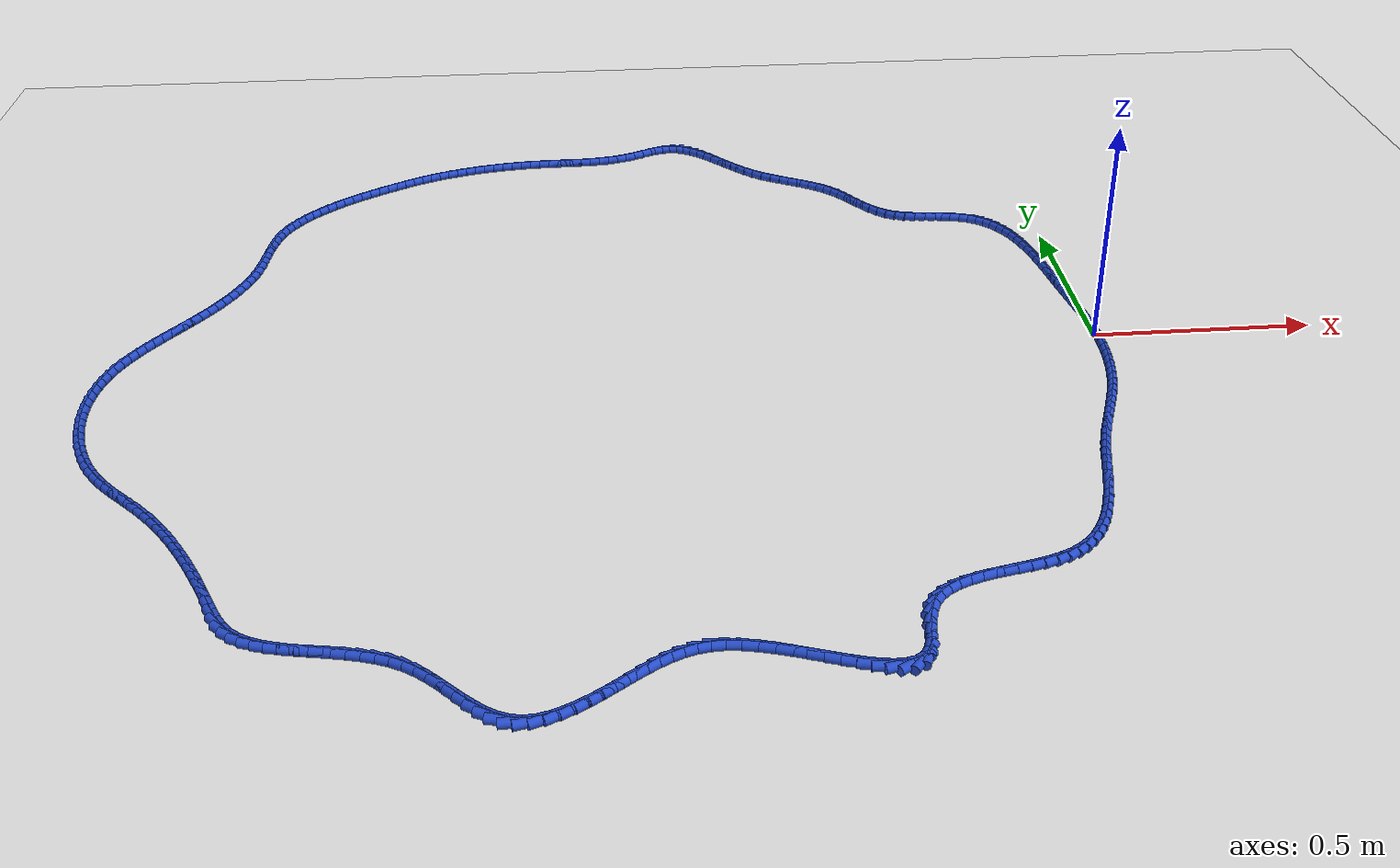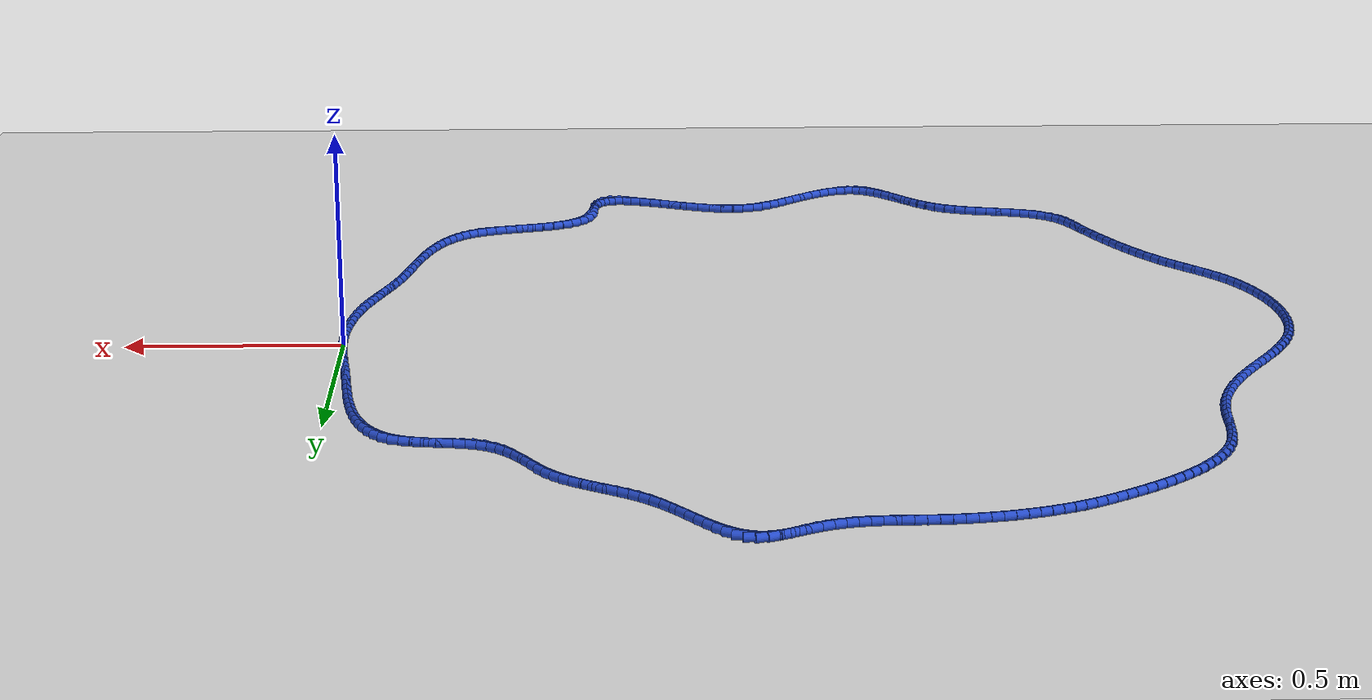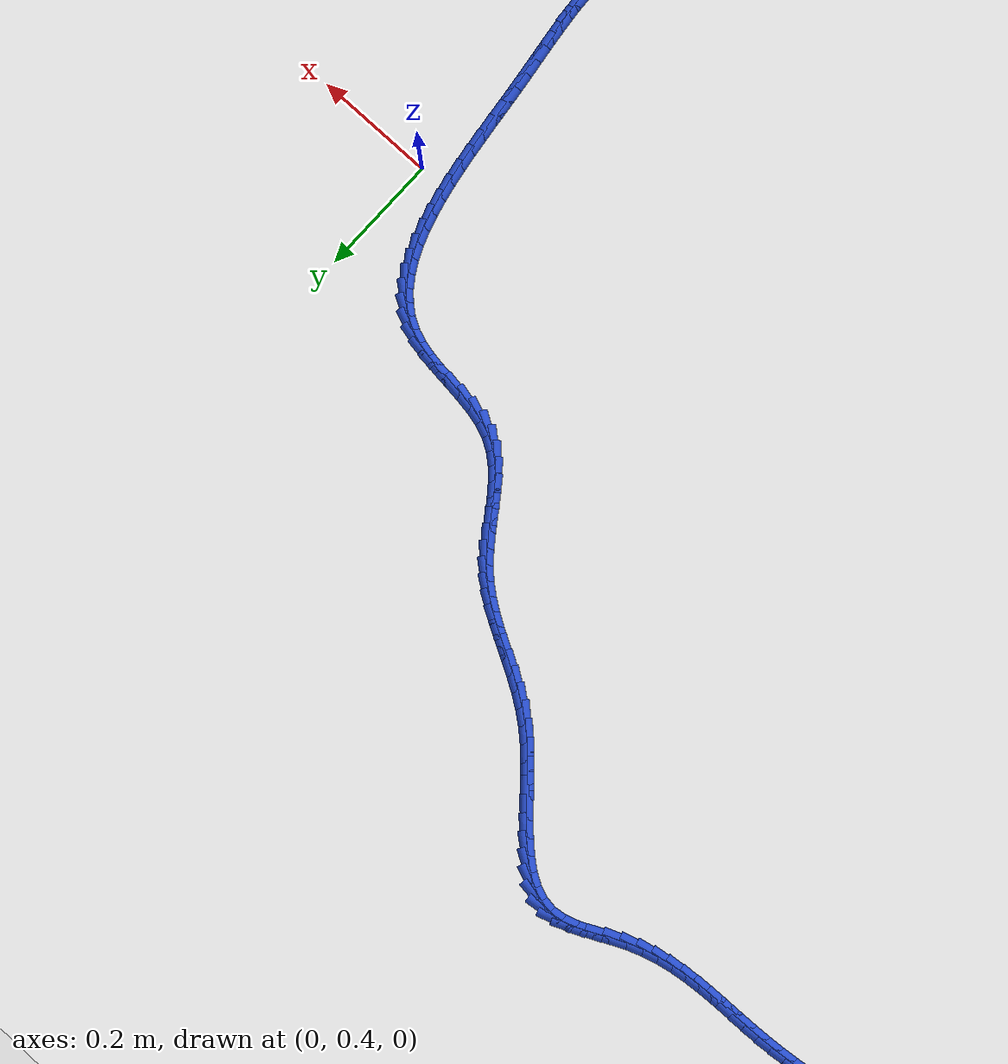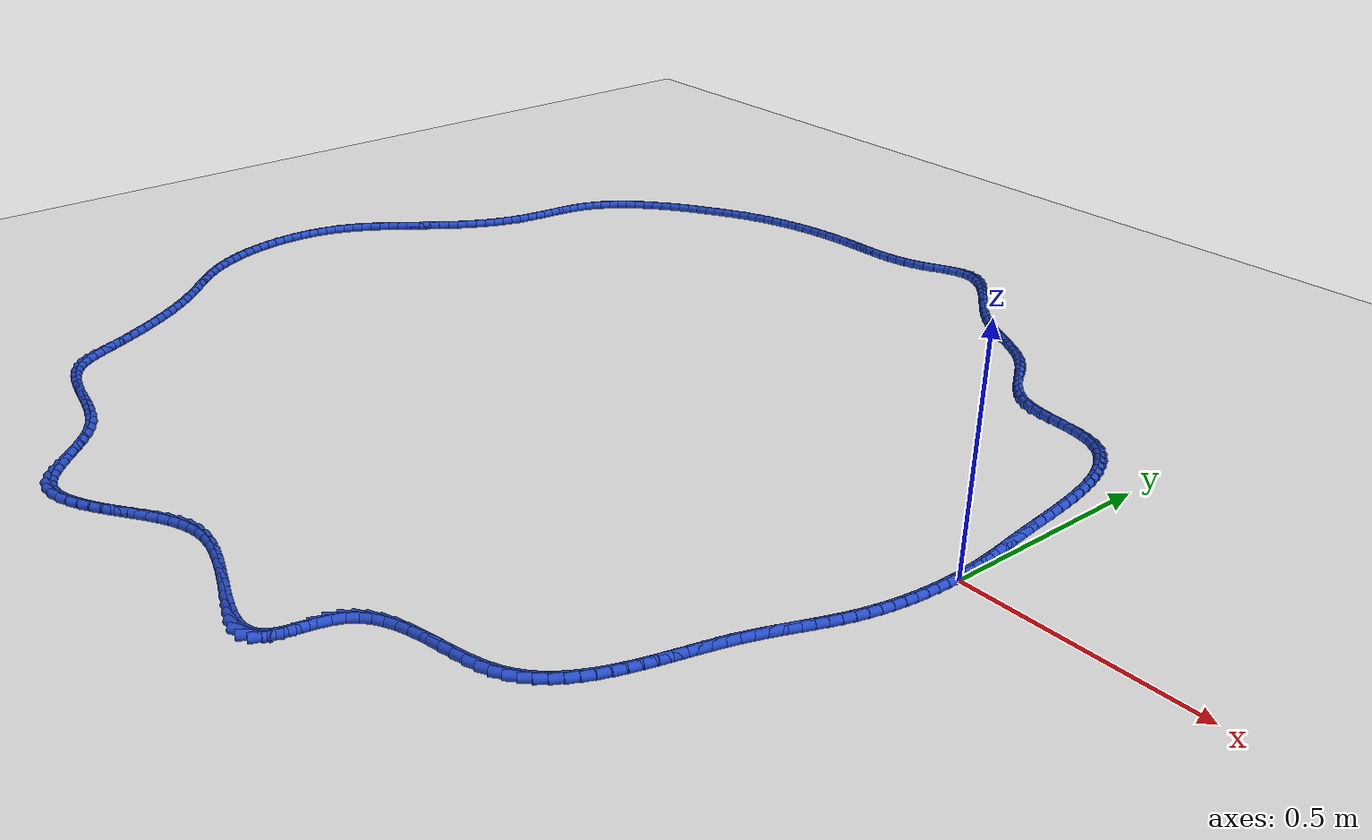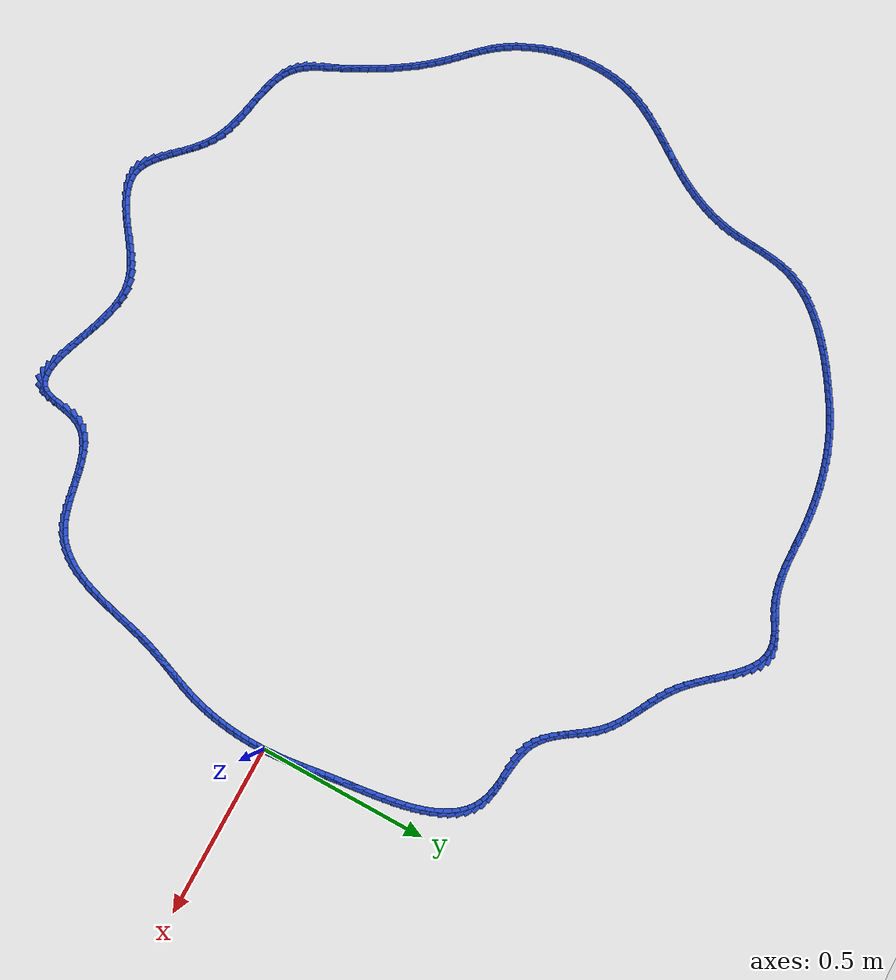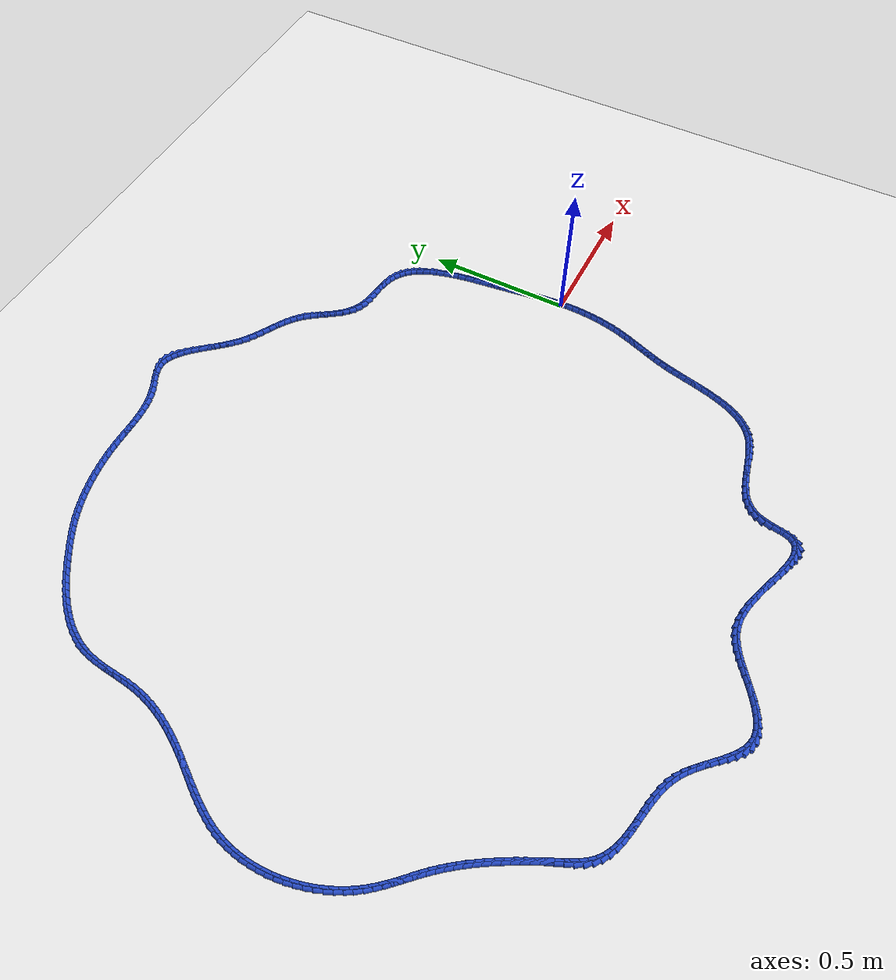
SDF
<sdf version="1.6">
 <world name="default">
  <light name="sun" type="directional">
   <pose>0 0 10 0 -0 0</pose>
   <diffuse>0.8 0.8 0.8 1</diffuse>
   <specular>0.2 0.2 0.2 1</specular>
   <attenuation>
    <range>1000</range>
    <constant>0.9</constant>
    <linear>0.01</linear>
    <quadratic>0.001</quadratic>
   </attenuation>
   <direction>-0.5 0.1 -0.9</direction>
  </light>
  <model name="ground_plane">
   <static>1</static>
   <link name="link">
    <collision name="collision">
     <geometry><plane><normal>0 0 1</normal><size>100 100</size></plane></geometry>
     <surface><friction><ode><mu>100</mu><mu2>50</mu2></ode></friction></surface>
    </collision>
    <visual name="visual">
     <cast_shadows>0</cast_shadows>
     <geometry><plane><normal>0 0 1</normal><size>100 100</size></plane></geometry>
     <material>
      <script><uri>file://media/materials/scripts/gazebo.material</uri><name>Gazebo/WhiteGlow</name></script>
     </material>
    </visual>
   </link>
  </model>
  <gravity>0 0 -9.8</gravity>
  <magnetic_field>6e-06 2.3e-05 -4.2e-05</magnetic_field>
  <atmosphere type="adiabatic"/>
  <physics name="default_physics" default="0" type="ode">
   <max_step_size>0.001</max_step_size>
   <real_time_factor>1</real_time_factor>
   <real_time_update_rate>1000</real_time_update_rate>
  </physics>
  <scene><ambient>0.4 0.4 0.4 1</ambient><background>0.7 0.7 0.7 1</background><shadows>1</shadows></scene>
  <spherical_coordinates>
   <surface_model>EARTH_WGS84</surface_model>
   <latitude_deg>0</latitude_deg>
   <longitude_deg>0</longitude_deg>
   <elevation>0</elevation>
   <heading_deg>0</heading_deg>
  </spherical_coordinates>
  <model name="line">
   <link name="link_0">
    <pose>8.673617379884035e-19 -3.469446951953614e-17 0.01 0 1.57 -1.5240641853317218</pose>
    <collision name="collision">
     <geometry><cylinder><radius>0.01</radius><length>0.08</length></cylinder></geometry>
    </collision>
    <visual name="visual">
     <material>
      <script><name>Gazebo/Blue</name><uri>file://media/materials/scripts/gazebo.material</uri></script>
     </material>
     <geometry><cylinder><radius>0.01</radius><length>0.08</length></cylinder></geometry>
    </visual>
   </link>
   <link name="link_1">
    <pose>-0.0011370628850971864 0.02431378036060707 0.01 0 1.57 -1.4969305123686296</pose>
    <collision name="collision">
     <geometry><cylinder><radius>0.01</radius><length>0.08</length></cylinder></geometry>
    </collision>
    <visual name="visual">
     <material>
      <script><name>Gazebo/Blue</name><uri>file://media/materials/scripts/gazebo.material</uri></script>
     </material>
     <geometry><cylinder><radius>0.01</radius><length>0.08</length></cylinder></geometry>
    </visual>
   </link>
   <link name="link_2">
    <pose>-0.002921043157018145 0.04842147544550481 0.01 0 1.57 -1.4741336956507662</pose>
    <collision name="collision">
     <geometry><cylinder><radius>0.01</radius><length>0.08</length></cylinder></geometry>
    </collision>
    <visual name="visual">
     <material>
      <script><name>Gazebo/Blue</name><uri>file://media/materials/scripts/gazebo.material</uri></script>
     </material>
     <geometry><cylinder><radius>0.01</radius><length>0.08</length></cylinder></geometry>
    </visual>
   </link>
   <link name="link_3">
    <pose>-0.005251955962243914 0.07246022233203431 0.01 0 1.57 -1.456071559786414</pose>
    <collision name="collision">
     <geometry><cylinder><radius>0.01</radius><length>0.08</length></cylinder></geometry>
    </collision>
    <visual name="visual">
     <material>
      <script><name>Gazebo/Blue</name><uri>file://media/materials/scripts/gazebo.material</uri></script>
     </material>
     <geometry><cylinder><radius>0.01</radius><length>0.08</length></cylinder></geometry>
    </visual>
   </link>
   <link name="link_4">
    <pose>-0.008029816447255542 0.09656715809753673 0.01 0 1.57 -1.442968445503576</pose>
    <collision name="collision">
     <geometry><cylinder><radius>0.01</radius><length>0.08</length></cylinder></geometry>
    </collision>
    <visual name="visual">
     <material>
      <script><name>Gazebo/Blue</name><uri>file://media/materials/scripts/gazebo.material</uri></script>
     </material>
     <geometry><cylinder><radius>0.01</radius><length>0.08</length></cylinder></geometry>
    </visual>
   </link>
   <link name="link_5">
    <pose>-0.011154639758534073 0.12087941981935318 0.01 0 1.57 -1.4348786645264213</pose>
    <collision name="collision">
     <geometry><cylinder><radius>0.01</radius><length>0.08</length></cylinder></geometry>
    </collision>
    <visual name="visual">
     <material>
      <script><name>Gazebo/Blue</name><uri>file://media/materials/scripts/gazebo.material</uri></script>
     </material>
     <geometry><cylinder><radius>0.01</radius><length>0.08</length></cylinder></geometry>
    </visual>
   </link>
   <link name="link_6">
    <pose>-0.014526441042560555 0.14553414457482483 0.01 0 1.57 -1.4317008175939747</pose>
    <collision name="collision">
     <geometry><cylinder><radius>0.01</radius><length>0.08</length></cylinder></geometry>
    </collision>
    <visual name="visual">
     <material>
      <script><name>Gazebo/Blue</name><uri>file://media/materials/scripts/gazebo.material</uri></script>
     </material>
     <geometry><cylinder><radius>0.01</radius><length>0.08</length></cylinder></geometry>
    </visual>
   </link>
   <link name="link_7">
    <pose>-0.01804523544581602 0.17066846944129266 0.01 0 1.57 -1.433199264471176</pose>
    <collision name="collision">
     <geometry><cylinder><radius>0.01</radius><length>0.08</length></cylinder></geometry>
    </collision>
    <visual name="visual">
     <material>
      <script><name>Gazebo/Blue</name><uri>file://media/materials/scripts/gazebo.material</uri></script>
     </material>
     <geometry><cylinder><radius>0.01</radius><length>0.08</length></cylinder></geometry>
    </visual>
   </link>
   <link name="link_8">
    <pose>-0.02161103811478153 0.19641953149609803 0.01 0 1.57 -1.4390294683640523</pose>
    <collision name="collision">
     <geometry><cylinder><radius>0.01</radius><length>0.08</length></cylinder></geometry>
    </collision>
    <visual name="visual">
     <material>
      <script><name>Gazebo/Blue</name><uri>file://media/materials/scripts/gazebo.material</uri></script>
     </material>
     <geometry><cylinder><radius>0.01</radius><length>0.08</length></cylinder></geometry>
    </visual>
   </link>
   <link name="link_9">
    <pose>-0.02512386433749043 0.2229244676020097 0.01 0 1.57 -1.4468864666676833</pose>
    <collision name="collision">
     <geometry><cylinder><radius>0.01</radius><length>0.08</length></cylinder></geometry>
    </collision>
    <visual name="visual">
     <material>
      <script><name>Gazebo/Blue</name><uri>file://media/materials/scripts/gazebo.material</uri></script>
     </material>
     <geometry><cylinder><radius>0.01</radius><length>0.08</length></cylinder></geometry>
    </visual>
   </link>
   <link name="link_10">
    <pose>-0.028527676028604204 0.25025379809651976 0.01 0 1.57 -1.4495886288142459</pose>
    <collision name="collision">
     <geometry><cylinder><radius>0.01</radius><length>0.08</length></cylinder></geometry>
    </collision>
    <visual name="visual">
     <material>
      <script><name>Gazebo/Blue</name><uri>file://media/materials/scripts/gazebo.material</uri></script>
     </material>
     <geometry><cylinder><radius>0.01</radius><length>0.08</length></cylinder></geometry>
    </visual>
   </link>
   <link name="link_11">
    <pose>-0.03193449382158683 0.27822329138851665 0.01 0 1.57 -1.4458705437820714</pose>
    <collision name="collision">
     <geometry><cylinder><radius>0.01</radius><length>0.08</length></cylinder></geometry>
    </collision>
    <visual name="visual">
     <material>
      <script><name>Gazebo/Blue</name><uri>file://media/materials/scripts/gazebo.material</uri></script>
     </material>
     <geometry><cylinder><radius>0.01</radius><length>0.08</length></cylinder></geometry>
    </visual>
   </link>
   <link name="link_12">
    <pose>-0.03549650529441764 0.30658782879543484 0.01 0 1.57 -1.4359208763719873</pose>
    <collision name="collision">
     <geometry><cylinder><radius>0.01</radius><length>0.08</length></cylinder></geometry>
    </collision>
    <visual name="visual">
     <material>
      <script><name>Gazebo/Blue</name><uri>file://media/materials/scripts/gazebo.material</uri></script>
     </material>
     <geometry><cylinder><radius>0.01</radius><length>0.08</length></cylinder></geometry>
    </visual>
   </link>
   <link name="link_13">
    <pose>-0.03936589802507603 0.33510229163470856 0.01 0 1.57 -1.4196334460924684</pose>
    <collision name="collision">
     <geometry><cylinder><radius>0.01</radius><length>0.08</length></cylinder></geometry>
    </collision>
    <visual name="visual">
     <material>
      <script><name>Gazebo/Blue</name><uri>file://media/materials/scripts/gazebo.material</uri></script>
     </material>
     <geometry><cylinder><radius>0.01</radius><length>0.08</length></cylinder></geometry>
    </visual>
   </link>
   <link name="link_14">
    <pose>-0.043694859591541325 0.3635215612237722 0.01 0 1.57 -1.3966212528681958</pose>
    <collision name="collision">
     <geometry><cylinder><radius>0.01</radius><length>0.08</length></cylinder></geometry>
    </collision>
    <visual name="visual">
     <material>
      <script><name>Gazebo/Blue</name><uri>file://media/materials/scripts/gazebo.material</uri></script>
     </material>
     <geometry><cylinder><radius>0.01</radius><length>0.08</length></cylinder></geometry>
    </visual>
   </link>
   <link name="link_15">
    <pose>-0.04863557757179294 0.3916005188800602 0.01 0 1.57 -1.3662082787203482</pose>
    <collision name="collision">
     <geometry><cylinder><radius>0.01</radius><length>0.08</length></cylinder></geometry>
    </collision>
    <visual name="visual">
     <material>
      <script><name>Gazebo/Blue</name><uri>file://media/materials/scripts/gazebo.material</uri></script>
     </material>
     <geometry><cylinder><radius>0.01</radius><length>0.08</length></cylinder></geometry>
    </visual>
   </link>
   <link name="link_16">
    <pose>-0.05434023954381022 0.41909404592100685 0.01 0 1.57 -1.327405013645648</pose>
    <collision name="collision">
     <geometry><cylinder><radius>0.01</radius><length>0.08</length></cylinder></geometry>
    </collision>
    <visual name="visual">
     <material>
      <script><name>Gazebo/Blue</name><uri>file://media/materials/scripts/gazebo.material</uri></script>
     </material>
     <geometry><cylinder><radius>0.01</radius><length>0.08</length></cylinder></geometry>
    </visual>
   </link>
   <link name="link_17">
    <pose>-0.06096103308557255 0.4457570236640466 0.01 0 1.57 -1.2788763596056034</pose>
    <collision name="collision">
     <geometry><cylinder><radius>0.01</radius><length>0.08</length></cylinder></geometry>
    </collision>
    <visual name="visual">
     <material>
      <script><name>Gazebo/Blue</name><uri>file://media/materials/scripts/gazebo.material</uri></script>
     </material>
     <geometry><cylinder><radius>0.01</radius><length>0.08</length></cylinder></geometry>
    </visual>
   </link>
   <link name="link_18">
    <pose>-0.06865014577505923 0.4713443334266137 0.01 0 1.57 -1.218919538011833</pose>
    <collision name="collision">
     <geometry><cylinder><radius>0.01</radius><length>0.08</length></cylinder></geometry>
    </collision>
    <visual name="visual">
     <material>
      <script><name>Gazebo/Blue</name><uri>file://media/materials/scripts/gazebo.material</uri></script>
     </material>
     <geometry><cylinder><radius>0.01</radius><length>0.08</length></cylinder></geometry>
    </visual>
   </link>
   <link name="link_19">
    <pose>-0.07755976519024974 0.4956108565261426 0.01 0 1.57 -1.1454893696384807</pose>
    <collision name="collision">
     <geometry><cylinder><radius>0.01</radius><length>0.08</length></cylinder></geometry>
    </collision>
    <visual name="visual">
     <material>
      <script><name>Gazebo/Blue</name><uri>file://media/materials/scripts/gazebo.material</uri></script>
     </material>
     <geometry><cylinder><radius>0.01</radius><length>0.08</length></cylinder></geometry>
    </visual>
   </link>
   <link name="link_20">
    <pose>-0.08784207890912335 0.5183114742800676 0.01 0 1.57 -1.0563437827675914</pose>
    <collision name="collision">
     <geometry><cylinder><radius>0.01</radius><length>0.08</length></cylinder></geometry>
    </collision>
    <visual name="visual">
     <material>
      <script><name>Gazebo/Blue</name><uri>file://media/materials/scripts/gazebo.material</uri></script>
     </material>
     <geometry><cylinder><radius>0.01</radius><length>0.08</length></cylinder></geometry>
    </visual>
   </link>
   <link name="link_21">
    <pose>-0.09964927450965946 0.5392010680058232 0.01 0 1.57 -0.949429680818018</pose>
    <collision name="collision">
     <geometry><cylinder><radius>0.01</radius><length>0.08</length></cylinder></geometry>
    </collision>
    <visual name="visual">
     <material>
      <script><name>Gazebo/Blue</name><uri>file://media/materials/scripts/gazebo.material</uri></script>
     </material>
     <geometry><cylinder><radius>0.01</radius><length>0.08</length></cylinder></geometry>
    </visual>
   </link>
   <link name="link_22">
    <pose>-0.11313353956983742 0.5580345190208432 0.01 0 1.57 -0.823647368579522</pose>
    <collision name="collision">
     <geometry><cylinder><radius>0.01</radius><length>0.08</length></cylinder></geometry>
    </collision>
    <visual name="visual">
     <material>
      <script><name>Gazebo/Blue</name><uri>file://media/materials/scripts/gazebo.material</uri></script>
     </material>
     <geometry><cylinder><radius>0.01</radius><length>0.08</length></cylinder></geometry>
    </visual>
   </link>
   <link name="link_23">
    <pose>-0.12844706166763664 0.5745667086425627 0.01 0 1.57 -0.6800013277637227</pose>
    <collision name="collision">
     <geometry><cylinder><radius>0.01</radius><length>0.08</length></cylinder></geometry>
    </collision>
    <visual name="visual">
     <material>
      <script><name>Gazebo/Blue</name><uri>file://media/materials/scripts/gazebo.material</uri></script>
     </material>
     <geometry><cylinder><radius>0.01</radius><length>0.08</length></cylinder></geometry>
    </visual>
   </link>
   <link name="link_24">
    <pose>-0.14574202838103645 0.5885525181884157 0.01 0 1.57 -0.5227183362739126</pose>
    <collision name="collision">
     <geometry><cylinder><radius>0.01</radius><length>0.08</length></cylinder></geometry>
    </collision>
    <visual name="visual">
     <material>
      <script><name>Gazebo/Blue</name><uri>file://media/materials/scripts/gazebo.material</uri></script>
     </material>
     <geometry><cylinder><radius>0.01</radius><length>0.08</length></cylinder></geometry>
    </visual>
   </link>
   <link name="link_25">
    <pose>-0.16517062728801626 0.5997468289758368 0.01 0 1.57 -0.3618012500604357</pose>
    <collision name="collision">
     <geometry><cylinder><radius>0.01</radius><length>0.08</length></cylinder></geometry>
    </collision>
    <visual name="visual">
     <material>
      <script><name>Gazebo/Blue</name><uri>file://media/materials/scripts/gazebo.material</uri></script>
     </material>
     <geometry><cylinder><radius>0.01</radius><length>0.08</length></cylinder></geometry>
    </visual>
   </link>
   <link name="link_26">
    <pose>-0.18685274004629196 0.6079526565183013 0.01 0 1.57 -0.23480176617950946</pose>
    <collision name="collision">
     <geometry><cylinder><radius>0.01</radius><length>0.08</length></cylinder></geometry>
    </collision>
    <visual name="visual">
     <material>
      <script><name>Gazebo/Blue</name><uri>file://media/materials/scripts/gazebo.material</uri></script>
     </material>
     <geometry><cylinder><radius>0.01</radius><length>0.08</length></cylinder></geometry>
    </visual>
   </link>
   <link name="link_27">
    <pose>-0.21048373252312055 0.6136055235017792 0.01 0 1.57 -0.15806391099328396</pose>
    <collision name="collision">
     <geometry><cylinder><radius>0.01</radius><length>0.08</length></cylinder></geometry>
    </collision>
    <visual name="visual">
     <material>
      <script><name>Gazebo/Blue</name><uri>file://media/materials/scripts/gazebo.material</uri></script>
     </material>
     <geometry><cylinder><radius>0.01</radius><length>0.08</length></cylinder></geometry>
    </visual>
   </link>
   <link name="link_28">
    <pose>-0.2354598932101858 0.6175865628567427 0.01 0 1.57 -0.1238086833445902</pose>
    <collision name="collision">
     <geometry><cylinder><radius>0.01</radius><length>0.08</length></cylinder></geometry>
    </collision>
    <visual name="visual">
     <material>
      <script><name>Gazebo/Blue</name><uri>file://media/materials/scripts/gazebo.material</uri></script>
     </material>
     <geometry><cylinder><radius>0.01</radius><length>0.08</length></cylinder></geometry>
    </visual>
   </link>
   <link name="link_29">
    <pose>-0.261171261112879 0.6207862189338571 0.01 0 1.57 -0.12736983379874356</pose>
    <collision name="collision">
     <geometry><cylinder><radius>0.01</radius><length>0.08</length></cylinder></geometry>
    </collision>
    <visual name="visual">
     <material>
      <script><name>Gazebo/Blue</name><uri>file://media/materials/scripts/gazebo.material</uri></script>
     </material>
     <geometry><cylinder><radius>0.01</radius><length>0.08</length></cylinder></geometry>
    </visual>
   </link>
   <link name="link_30">
    <pose>-0.28700787523659194 0.6240949360837877 0.01 0 1.57 -0.16832880544252976</pose>
    <collision name="collision">
     <geometry><cylinder><radius>0.01</radius><length>0.08</length></cylinder></geometry>
    </collision>
    <visual name="visual">
     <material>
      <script><name>Gazebo/Blue</name><uri>file://media/materials/scripts/gazebo.material</uri></script>
     </material>
     <geometry><cylinder><radius>0.01</radius><length>0.08</length></cylinder></geometry>
    </visual>
   </link>
   <link name="link_31">
    <pose>-0.31235977458671604 0.6284031586572006 0.01 0 1.57 -0.25016587829168807</pose>
    <collision name="collision">
     <geometry><cylinder><radius>0.01</radius><length>0.08</length></cylinder></geometry>
    </collision>
    <visual name="visual">
     <material>
      <script><name>Gazebo/Blue</name><uri>file://media/materials/scripts/gazebo.material</uri></script>
     </material>
     <geometry><cylinder><radius>0.01</radius><length>0.08</length></cylinder></geometry>
    </visual>
   </link>
   <link name="link_32">
    <pose>-0.3366169981686428 0.6346013310047612 0.01 0 1.57 -0.3788819816051231</pose>
    <collision name="collision">
     <geometry><cylinder><radius>0.01</radius><length>0.08</length></cylinder></geometry>
    </collision>
    <visual name="visual">
     <material>
      <script><name>Gazebo/Blue</name><uri>file://media/materials/scripts/gazebo.material</uri></script>
     </material>
     <geometry><cylinder><radius>0.01</radius><length>0.08</length></cylinder></geometry>
    </visual>
   </link>
   <link name="link_33">
    <pose>-0.3591695849877641 0.6435798974771353 0.01 0 1.57 -0.5522684606557956</pose>
    <collision name="collision">
     <geometry><cylinder><radius>0.01</radius><length>0.08</length></cylinder></geometry>
    </collision>
    <visual name="visual">
     <material>
      <script><name>Gazebo/Blue</name><uri>file://media/materials/scripts/gazebo.material</uri></script>
     </material>
     <geometry><cylinder><radius>0.01</radius><length>0.08</length></cylinder></geometry>
    </visual>
   </link>
   <link name="link_34">
    <pose>-0.37949132501001354 0.6561027782904382 0.01 0 1.57 -0.7136770003450927</pose>
    <collision name="collision">
     <geometry><cylinder><radius>0.01</radius><length>0.08</length></cylinder></geometry>
    </collision>
    <visual name="visual">
     <material>
      <script><name>Gazebo/Blue</name><uri>file://media/materials/scripts/gazebo.material</uri></script>
     </material>
     <geometry><cylinder><radius>0.01</radius><length>0.08</length></cylinder></geometry>
    </visual>
   </link>
   <link name="link_35">
    <pose>-0.39773810367896434 0.671903439330115 0.01 0 1.57 -0.8325441333770828</pose>
    <collision name="collision">
     <geometry><cylinder><radius>0.01</radius><length>0.08</length></cylinder></geometry>
    </collision>
    <visual name="visual">
     <material>
      <script><name>Gazebo/Blue</name><uri>file://media/materials/scripts/gazebo.material</uri></script>
     </material>
     <geometry><cylinder><radius>0.01</radius><length>0.08</length></cylinder></geometry>
    </visual>
   </link>
   <link name="link_36">
    <pose>-0.4143980984785112 0.6902133467129241 0.01 0 1.57 -0.9106454678530164</pose>
    <collision name="collision">
     <geometry><cylinder><radius>0.01</radius><length>0.08</length></cylinder></geometry>
    </collision>
    <visual name="visual">
     <material>
      <script><name>Gazebo/Blue</name><uri>file://media/materials/scripts/gazebo.material</uri></script>
     </material>
     <geometry><cylinder><radius>0.01</radius><length>0.08</length></cylinder></geometry>
    </visual>
   </link>
   <link name="link_37">
    <pose>-0.42996171600053956 0.7102605990007033 0.01 0 1.57 -0.9521691379988743</pose>
    <collision name="collision">
     <geometry><cylinder><radius>0.01</radius><length>0.08</length></cylinder></geometry>
    </collision>
    <visual name="visual">
     <material>
      <script><name>Gazebo/Blue</name><uri>file://media/materials/scripts/gazebo.material</uri></script>
     </material>
     <geometry><cylinder><radius>0.01</radius><length>0.08</length></cylinder></geometry>
    </visual>
   </link>
   <link name="link_38">
    <pose>-0.44491936283693456 0.7312732947552895 0.01 0 1.57 -0.9601426414158248</pose>
    <collision name="collision">
     <geometry><cylinder><radius>0.01</radius><length>0.08</length></cylinder></geometry>
    </collision>
    <visual name="visual">
     <material>
      <script><name>Gazebo/Blue</name><uri>file://media/materials/scripts/gazebo.material</uri></script>
     </material>
     <geometry><cylinder><radius>0.01</radius><length>0.08</length></cylinder></geometry>
    </visual>
   </link>
   <link name="link_39">
    <pose>-0.45976144557958193 0.75247953253852 0.01 0 1.57 -0.9352219871458216</pose>
    <collision name="collision">
     <geometry><cylinder><radius>0.01</radius><length>0.08</length></cylinder></geometry>
    </collision>
    <visual name="visual">
     <material>
      <script><name>Gazebo/Blue</name><uri>file://media/materials/scripts/gazebo.material</uri></script>
     </material>
     <geometry><cylinder><radius>0.01</radius><length>0.08</length></cylinder></geometry>
    </visual>
   </link>
   <link name="link_40">
    <pose>-0.4749783708203664 0.7731074109122318 0.01 0 1.57 -0.8755227579774498</pose>
    <collision name="collision">
     <geometry><cylinder><radius>0.01</radius><length>0.08</length></cylinder></geometry>
    </collision>
    <visual name="visual">
     <material>
      <script><name>Gazebo/Blue</name><uri>file://media/materials/scripts/gazebo.material</uri></script>
     </material>
     <geometry><cylinder><radius>0.01</radius><length>0.08</length></cylinder></geometry>
    </visual>
   </link>
   <link name="link_41">
    <pose>-0.49106054515117414 0.7923850284382626 0.01 0 1.57 -0.7812546522800257</pose>
    <collision name="collision">
     <geometry><cylinder><radius>0.01</radius><length>0.08</length></cylinder></geometry>
    </collision>
    <visual name="visual">
     <material>
      <script><name>Gazebo/Blue</name><uri>file://media/materials/scripts/gazebo.material</uri></script>
     </material>
     <geometry><cylinder><radius>0.01</radius><length>0.08</length></cylinder></geometry>
    </visual>
   </link>
   <link name="link_42">
    <pose>-0.508447459562861 0.8096284508431593 0.01 0 1.57 -0.6855163507687315</pose>
    <collision name="collision">
     <geometry><cylinder><radius>0.01</radius><length>0.08</length></cylinder></geometry>
    </collision>
    <visual name="visual">
     <material>
      <script><name>Gazebo/Blue</name><uri>file://media/materials/scripts/gazebo.material</uri></script>
     </material>
     <geometry><cylinder><radius>0.01</radius><length>0.08</length></cylinder></geometry>
    </visual>
   </link>
   <link name="link_43">
    <pose>-0.5271383607761979 0.8249143563069513 0.01 0 1.57 -0.6092476882218621</pose>
    <collision name="collision">
     <geometry><cylinder><radius>0.01</radius><length>0.08</length></cylinder></geometry>
    </collision>
    <visual name="visual">
     <material>
      <script><name>Gazebo/Blue</name><uri>file://media/materials/scripts/gazebo.material</uri></script>
     </material>
     <geometry><cylinder><radius>0.01</radius><length>0.08</length></cylinder></geometry>
    </visual>
   </link>
   <link name="link_44">
    <pose>-0.5469070441694293 0.8387089365375723 0.01 0 1.57 -0.5546163647159799</pose>
    <collision name="collision">
     <geometry><cylinder><radius>0.01</radius><length>0.08</length></cylinder></geometry>
    </collision>
    <visual name="visual">
     <material>
      <script><name>Gazebo/Blue</name><uri>file://media/materials/scripts/gazebo.material</uri></script>
     </material>
     <geometry><cylinder><radius>0.01</radius><length>0.08</length></cylinder></geometry>
    </visual>
   </link>
   <link name="link_45">
    <pose>-0.5675254782124305 0.8514815396026194 0.01 0 1.57 -0.5220778849564481</pose>
    <collision name="collision">
     <geometry><cylinder><radius>0.01</radius><length>0.08</length></cylinder></geometry>
    </collision>
    <visual name="visual">
     <material>
      <script><name>Gazebo/Blue</name><uri>file://media/materials/scripts/gazebo.material</uri></script>
     </material>
     <geometry><cylinder><radius>0.01</radius><length>0.08</length></cylinder></geometry>
    </visual>
   </link>
   <link name="link_46">
    <pose>-0.5887656313750774 0.8637015135696897 0.01 0 1.57 -0.5112530709110095</pose>
    <collision name="collision">
     <geometry><cylinder><radius>0.01</radius><length>0.08</length></cylinder></geometry>
    </collision>
    <visual name="visual">
     <material>
      <script><name>Gazebo/Blue</name><uri>file://media/materials/scripts/gazebo.material</uri></script>
     </material>
     <geometry><cylinder><radius>0.01</radius><length>0.08</length></cylinder></geometry>
    </visual>
   </link>
   <link name="link_47">
    <pose>-0.6103994721272457 0.8758382065063804 0.01 0 1.57 -0.5214221881753405</pose>
    <collision name="collision">
     <geometry><cylinder><radius>0.01</radius><length>0.08</length></cylinder></geometry>
    </collision>
    <visual name="visual">
     <material>
      <script><name>Gazebo/Blue</name><uri>file://media/materials/scripts/gazebo.material</uri></script>
     </material>
     <geometry><cylinder><radius>0.01</radius><length>0.08</length></cylinder></geometry>
    </visual>
   </link>
   <link name="link_48">
    <pose>-0.6321989689388107 0.888360966480289 0.01 0 1.57 -0.5517045330967456</pose>
    <collision name="collision">
     <geometry><cylinder><radius>0.01</radius><length>0.08</length></cylinder></geometry>
    </collision>
    <visual name="visual">
     <material>
      <script><name>Gazebo/Blue</name><uri>file://media/materials/scripts/gazebo.material</uri></script>
     </material>
     <geometry><cylinder><radius>0.01</radius><length>0.08</length></cylinder></geometry>
    </visual>
   </link>
   <link name="link_49">
    <pose>-0.6539360902796483 0.9017391415590124 0.01 0 1.57 -0.6009665458183779</pose>
    <collision name="collision">
     <geometry><cylinder><radius>0.01</radius><length>0.08</length></cylinder></geometry>
    </collision>
    <visual name="visual">
     <material>
      <script><name>Gazebo/Blue</name><uri>file://media/materials/scripts/gazebo.material</uri></script>
     </material>
     <geometry><cylinder><radius>0.01</radius><length>0.08</length></cylinder></geometry>
    </visual>
   </link>
   <link name="link_50">
    <pose>-0.675382804619634 0.9164420798101476 0.01 0 1.57 -0.6675450351098691</pose>
    <collision name="collision">
     <geometry><cylinder><radius>0.01</radius><length>0.08</length></cylinder></geometry>
    </collision>
    <visual name="visual">
     <material>
      <script><name>Gazebo/Blue</name><uri>file://media/materials/scripts/gazebo.material</uri></script>
     </material>
     <geometry><cylinder><radius>0.01</radius><length>0.08</length></cylinder></geometry>
    </visual>
   </link>
   <link name="link_51">
    <pose>-0.6963110804286436 0.9329391293012925 0.01 0 1.57 -0.74435445503672</pose>
    <collision name="collision">
     <geometry><cylinder><radius>0.01</radius><length>0.08</length></cylinder></geometry>
    </collision>
    <visual name="visual">
     <material>
      <script><name>Gazebo/Blue</name><uri>file://media/materials/scripts/gazebo.material</uri></script>
     </material>
     <geometry><cylinder><radius>0.01</radius><length>0.08</length></cylinder></geometry>
    </visual>
   </link>
   <link name="link_52">
    <pose>-0.7165351687375073 0.9515676657613552 0.01 0 1.57 -0.8038381061487639</pose>
    <collision name="collision">
     <geometry><cylinder><radius>0.01</radius><length>0.08</length></cylinder></geometry>
    </collision>
    <visual name="visual">
     <material>
      <script><name>Gazebo/Blue</name><uri>file://media/materials/scripts/gazebo.material</uri></script>
     </material>
     <geometry><cylinder><radius>0.01</radius><length>0.08</length></cylinder></geometry>
    </visual>
   </link>
   <link name="link_53">
    <pose>-0.736118606988165 0.9718869921172436 0.01 0 1.57 -0.8395240504170696</pose>
    <collision name="collision">
     <geometry><cylinder><radius>0.01</radius><length>0.08</length></cylinder></geometry>
    </collision>
    <visual name="visual">
     <material>
      <script><name>Gazebo/Blue</name><uri>file://media/materials/scripts/gazebo.material</uri></script>
     </material>
     <geometry><cylinder><radius>0.01</radius><length>0.08</length></cylinder></geometry>
    </visual>
   </link>
   <link name="link_54">
    <pose>-0.7552159768160801 0.9931722441387197 0.01 0 1.57 -0.8537884048432745</pose>
    <collision name="collision">
     <geometry><cylinder><radius>0.01</radius><length>0.08</length></cylinder></geometry>
    </collision>
    <visual name="visual">
     <material>
      <script><name>Gazebo/Blue</name><uri>file://media/materials/scripts/gazebo.material</uri></script>
     </material>
     <geometry><cylinder><radius>0.01</radius><length>0.08</length></cylinder></geometry>
    </visual>
   </link>
   <link name="link_55">
    <pose>-0.7739819939495041 1.0146981390651064 0.01 0 1.57 -0.8471875778381083</pose>
    <collision name="collision">
     <geometry><cylinder><radius>0.01</radius><length>0.08</length></cylinder></geometry>
    </collision>
    <visual name="visual">
     <material>
      <script><name>Gazebo/Blue</name><uri>file://media/materials/scripts/gazebo.material</uri></script>
     </material>
     <geometry><cylinder><radius>0.01</radius><length>0.08</length></cylinder></geometry>
    </visual>
   </link>
   <link name="link_56">
    <pose>-0.7925713741166878 1.0357393941357262 0.01 0 1.57 -0.818300694091995</pose>
    <collision name="collision">
     <geometry><cylinder><radius>0.01</radius><length>0.08</length></cylinder></geometry>
    </collision>
    <visual name="visual">
     <material>
      <script><name>Gazebo/Blue</name><uri>file://media/materials/scripts/gazebo.material</uri></script>
     </material>
     <geometry><cylinder><radius>0.01</radius><length>0.08</length></cylinder></geometry>
    </visual>
   </link>
   <link name="link_57">
    <pose>-0.8111388330458824 1.055570726589902 0.01 0 1.57 -0.7634288605119319</pose>
    <collision name="collision">
     <geometry><cylinder><radius>0.01</radius><length>0.08</length></cylinder></geometry>
    </collision>
    <visual name="visual">
     <material>
      <script><name>Gazebo/Blue</name><uri>file://media/materials/scripts/gazebo.material</uri></script>
     </material>
     <geometry><cylinder><radius>0.01</radius><length>0.08</length></cylinder></geometry>
    </visual>
   </link>
   <link name="link_58">
    <pose>-0.8298390864653388 1.0734668536669554 0.01 0 1.57 -0.6761980757981866</pose>
    <collision name="collision">
     <geometry><cylinder><radius>0.01</radius><length>0.08</length></cylinder></geometry>
    </collision>
    <visual name="visual">
     <material>
      <script><name>Gazebo/Blue</name><uri>file://media/materials/scripts/gazebo.material</uri></script>
     </material>
     <geometry><cylinder><radius>0.01</radius><length>0.08</length></cylinder></geometry>
    </visual>
   </link>
   <link name="link_59">
    <pose>-0.8488268501033088 1.0887024926062105 0.01 0 1.57 -0.5476490253191674</pose>
    <collision name="collision">
     <geometry><cylinder><radius>0.01</radius><length>0.08</length></cylinder></geometry>
    </collision>
    <visual name="visual">
     <material>
      <script><name>Gazebo/Blue</name><uri>file://media/materials/scripts/gazebo.material</uri></script>
     </material>
     <geometry><cylinder><radius>0.01</radius><length>0.08</length></cylinder></geometry>
    </visual>
   </link>
   <link name="link_60">
    <pose>-0.868256839688043 1.1005523606469891 0.01 0 1.57 -0.3687452747947741</pose>
    <collision name="collision">
     <geometry><cylinder><radius>0.01</radius><length>0.08</length></cylinder></geometry>
    </collision>
    <visual name="visual">
     <material>
      <script><name>Gazebo/Blue</name><uri>file://media/materials/scripts/gazebo.material</uri></script>
     </material>
     <geometry><cylinder><radius>0.01</radius><length>0.08</length></cylinder></geometry>
    </visual>
   </link>
   <link name="link_61">
    <pose>-0.8882837709477928 1.1082911750286142 0.01 0 1.57 -0.13878796552443057</pose>
    <collision name="collision">
     <geometry><cylinder><radius>0.01</radius><length>0.08</length></cylinder></geometry>
    </collision>
    <visual name="visual">
     <material>
      <script><name>Gazebo/Blue</name><uri>file://media/materials/scripts/gazebo.material</uri></script>
     </material>
     <geometry><cylinder><radius>0.01</radius><length>0.08</length></cylinder></geometry>
    </visual>
   </link>
   <link name="link_62">
    <pose>-0.9090623596108088 1.111193652990408 0.01 0 1.57 0.11703552913813763</pose>
    <collision name="collision">
     <geometry><cylinder><radius>0.01</radius><length>0.08</length></cylinder></geometry>
    </collision>
    <visual name="visual">
     <material>
      <script><name>Gazebo/Blue</name><uri>file://media/materials/scripts/gazebo.material</uri></script>
     </material>
     <geometry><cylinder><radius>0.01</radius><length>0.08</length></cylinder></geometry>
    </visual>
   </link>
   <link name="link_63">
    <pose>-0.9307326852191442 1.1086458114670585 0.01 0 1.57 0.31056202767811447</pose>
    <collision name="collision">
     <geometry><cylinder><radius>0.01</radius><length>0.08</length></cylinder></geometry>
    </collision>
    <visual name="visual">
     <material>
      <script><name>Gazebo/Blue</name><uri>file://media/materials/scripts/gazebo.material</uri></script>
     </material>
     <geometry><cylinder><radius>0.01</radius><length>0.08</length></cylinder></geometry>
    </visual>
   </link>
   <link name="link_64">
    <pose>-0.9532527777965989 1.1014180482454405 0.01 0 1.57 0.4141166912129083</pose>
    <collision name="collision">
     <geometry><cylinder><radius>0.01</radius><length>0.08</length></cylinder></geometry>
    </collision>
    <visual name="visual">
     <material>
      <script><name>Gazebo/Blue</name><uri>file://media/materials/scripts/gazebo.material</uri></script>
     </material>
     <geometry><cylinder><radius>0.01</radius><length>0.08</length></cylinder></geometry>
    </visual>
   </link>
   <link name="link_65">
    <pose>-0.9764573048554087 1.0912188613640994 0.01 0 1.57 0.4495090013999257</pose>
    <collision name="collision">
     <geometry><cylinder><radius>0.01</radius><length>0.08</length></cylinder></geometry>
    </collision>
    <visual name="visual">
     <material>
      <script><name>Gazebo/Blue</name><uri>file://media/materials/scripts/gazebo.material</uri></script>
     </material>
     <geometry><cylinder><radius>0.01</radius><length>0.08</length></cylinder></geometry>
    </visual>
   </link>
   <link name="link_66">
    <pose>-1.0001785951994475 1.0797745333803528 0.01 0 1.57 0.42738827881637964</pose>
    <collision name="collision">
     <geometry><cylinder><radius>0.01</radius><length>0.08</length></cylinder></geometry>
    </collision>
    <visual name="visual">
     <material>
      <script><name>Gazebo/Blue</name><uri>file://media/materials/scripts/gazebo.material</uri></script>
     </material>
     <geometry><cylinder><radius>0.01</radius><length>0.08</length></cylinder></geometry>
    </visual>
   </link>
   <link name="link_67">
    <pose>-1.0242489776325892 1.0688113468515177 0.01 0 1.57 0.3530320364232878</pose>
    <collision name="collision">
     <geometry><cylinder><radius>0.01</radius><length>0.08</length></cylinder></geometry>
    </collision>
    <visual name="visual">
     <material>
      <script><name>Gazebo/Blue</name><uri>file://media/materials/scripts/gazebo.material</uri></script>
     </material>
     <geometry><cylinder><radius>0.01</radius><length>0.08</length></cylinder></geometry>
    </visual>
   </link>
   <link name="link_68">
    <pose>-1.0485148059921094 1.0598701569910525 0.01 0 1.57 0.26759554136000435</pose>
    <collision name="collision">
     <geometry><cylinder><radius>0.01</radius><length>0.08</length></cylinder></geometry>
    </collision>
    <visual name="visual">
     <material>
      <script><name>Gazebo/Blue</name><uri>file://media/materials/scripts/gazebo.material</uri></script>
     </material>
     <geometry><cylinder><radius>0.01</radius><length>0.08</length></cylinder></geometry>
    </visual>
   </link>
   <link name="link_69">
    <pose>-1.0729217709770134 1.0531784695257589 0.01 0 1.57 0.19246781330782994</pose>
    <collision name="collision">
     <geometry><cylinder><radius>0.01</radius><length>0.08</length></cylinder></geometry>
    </collision>
    <visual name="visual">
     <material>
      <script><name>Gazebo/Blue</name><uri>file://media/materials/scripts/gazebo.material</uri></script>
     </material>
     <geometry><cylinder><radius>0.01</radius><length>0.08</length></cylinder></geometry>
    </visual>
   </link>
   <link name="link_70">
    <pose>-1.0974584515188963 1.0483967575897999 0.01 0 1.57 0.1296075258111395</pose>
    <collision name="collision">
     <geometry><cylinder><radius>0.01</radius><length>0.08</length></cylinder></geometry>
    </collision>
    <visual name="visual">
     <material>
      <script><name>Gazebo/Blue</name><uri>file://media/materials/scripts/gazebo.material</uri></script>
     </material>
     <geometry><cylinder><radius>0.01</radius><length>0.08</length></cylinder></geometry>
    </visual>
   </link>
   <link name="link_71">
    <pose>-1.122113596187889 1.0451832514974588 0.01 0 1.57 0.08007400746935366</pose>
    <collision name="collision">
     <geometry><cylinder><radius>0.01</radius><length>0.08</length></cylinder></geometry>
    </collision>
    <visual name="visual">
     <material>
      <script><name>Gazebo/Blue</name><uri>file://media/materials/scripts/gazebo.material</uri></script>
     </material>
     <geometry><cylinder><radius>0.01</radius><length>0.08</length></cylinder></geometry>
    </visual>
   </link>
   <link name="link_72">
    <pose>-1.146875953554125 1.0431961815630206 0.01 0 1.57 0.044318428447577295</pose>
    <collision name="collision">
     <geometry><cylinder><radius>0.01</radius><length>0.08</length></cylinder></geometry>
    </collision>
    <visual name="visual">
     <material>
      <script><name>Gazebo/Blue</name><uri>file://media/materials/scripts/gazebo.material</uri></script>
     </material>
     <geometry><cylinder><radius>0.01</radius><length>0.08</length></cylinder></geometry>
    </visual>
   </link>
   <link name="link_73">
    <pose>-1.1717342721877375 1.0420937781007695 0.01 0 1.57 0.022427623934136047</pose>
    <collision name="collision">
     <geometry><cylinder><radius>0.01</radius><length>0.08</length></cylinder></geometry>
    </collision>
    <visual name="visual">
     <material>
      <script><name>Gazebo/Blue</name><uri>file://media/materials/scripts/gazebo.material</uri></script>
     </material>
     <geometry><cylinder><radius>0.01</radius><length>0.08</length></cylinder></geometry>
    </visual>
   </link>
   <link name="link_74">
    <pose>-1.1966773006588576 1.0415342714249898 0.01 0 1.57 0.014324755647214705</pose>
    <collision name="collision">
     <geometry><cylinder><radius>0.01</radius><length>0.08</length></cylinder></geometry>
    </collision>
    <visual name="visual">
     <material>
      <script><name>Gazebo/Blue</name><uri>file://media/materials/scripts/gazebo.material</uri></script>
     </material>
     <geometry><cylinder><radius>0.01</radius><length>0.08</length></cylinder></geometry>
    </visual>
   </link>
   <link name="link_75">
    <pose>-1.2216937875376181 1.0411758918499658 0.01 0 1.57 0.01989562604277477</pose>
    <collision name="collision">
     <geometry><cylinder><radius>0.01</radius><length>0.08</length></cylinder></geometry>
    </collision>
    <visual name="visual">
     <material>
      <script><name>Gazebo/Blue</name><uri>file://media/materials/scripts/gazebo.material</uri></script>
     </material>
     <geometry><cylinder><radius>0.01</radius><length>0.08</length></cylinder></geometry>
    </visual>
   </link>
   <link name="link_76">
    <pose>-1.2467724813941523 1.0406768696899829 0.01 0 1.57 0.03883596168249597</pose>
    <collision name="collision">
     <geometry><cylinder><radius>0.01</radius><length>0.08</length></cylinder></geometry>
    </collision>
    <visual name="visual">
     <material>
      <script><name>Gazebo/Blue</name><uri>file://media/materials/scripts/gazebo.material</uri></script>
     </material>
     <geometry><cylinder><radius>0.01</radius><length>0.08</length></cylinder></geometry>
    </visual>
   </link>
   <link name="link_77">
    <pose>-1.2719016787282926 1.039700462212863 0.01 0 1.57 0.065244200546952</pose>
    <collision name="collision">
     <geometry><cylinder><radius>0.01</radius><length>0.08</length></cylinder></geometry>
    </collision>
    <visual name="visual">
     <material>
      <script><name>Gazebo/Blue</name><uri>file://media/materials/scripts/gazebo.material</uri></script>
     </material>
     <geometry><cylinder><radius>0.01</radius><length>0.08</length></cylinder></geometry>
    </visual>
   </link>
   <link name="link_78">
    <pose>-1.297056456487506 1.038056926114667 0.01 0 1.57 0.09255428253780851</pose>
    <collision name="collision">
     <geometry><cylinder><radius>0.01</radius><length>0.08</length></cylinder></geometry>
    </collision>
    <visual name="visual">
     <material>
      <script><name>Gazebo/Blue</name><uri>file://media/materials/scripts/gazebo.material</uri></script>
     </material>
     <geometry><cylinder><radius>0.01</radius><length>0.08</length></cylinder></geometry>
    </visual>
   </link>
   <link name="link_79">
    <pose>-1.3221968836090754 1.0357234049008235 0.01 0 1.57 0.120493697480449</pose>
    <collision name="collision">
     <geometry><cylinder><radius>0.01</radius><length>0.08</length></cylinder></geometry>
    </collision>
    <visual name="visual">
     <material>
      <script><name>Gazebo/Blue</name><uri>file://media/materials/scripts/gazebo.material</uri></script>
     </material>
     <geometry><cylinder><radius>0.01</radius><length>0.08</length></cylinder></geometry>
    </visual>
   </link>
   <link name="link_80">
    <pose>-1.3472822174621433 1.032686066592072 0.01 0 1.57 0.14914677674639065</pose>
    <collision name="collision">
     <geometry><cylinder><radius>0.01</radius><length>0.08</length></cylinder></geometry>
    </collision>
    <visual name="visual">
     <material>
      <script><name>Gazebo/Blue</name><uri>file://media/materials/scripts/gazebo.material</uri></script>
     </material>
     <geometry><cylinder><radius>0.01</radius><length>0.08</length></cylinder></geometry>
    </visual>
   </link>
   <link name="link_81">
    <pose>-1.3722717154158524 1.0289310792091553 0.01 0 1.57 0.17859733008699863</pose>
    <collision name="collision">
     <geometry><cylinder><radius>0.01</radius><length>0.08</length></cylinder></geometry>
    </collision>
    <visual name="visual">
     <material>
      <script><name>Gazebo/Blue</name><uri>file://media/materials/scripts/gazebo.material</uri></script>
     </material>
     <geometry><cylinder><radius>0.01</radius><length>0.08</length></cylinder></geometry>
    </visual>
   </link>
   <link name="link_82">
    <pose>-1.3971246348393451 1.0244446107728136 0.01 0 1.57 0.20892845728210982</pose>
    <collision name="collision">
     <geometry><cylinder><radius>0.01</radius><length>0.08</length></cylinder></geometry>
    </collision>
    <visual name="visual">
     <material>
      <script><name>Gazebo/Blue</name><uri>file://media/materials/scripts/gazebo.material</uri></script>
     </material>
     <geometry><cylinder><radius>0.01</radius><length>0.08</length></cylinder></geometry>
    </visual>
   </link>
   <link name="link_83">
    <pose>-1.4218002331017634 1.019212829303789 0.01 0 1.57 0.24022216380303857</pose>
    <collision name="collision">
     <geometry><cylinder><radius>0.01</radius><length>0.08</length></cylinder></geometry>
    </collision>
    <visual name="visual">
     <material>
      <script><name>Gazebo/Blue</name><uri>file://media/materials/scripts/gazebo.material</uri></script>
     </material>
     <geometry><cylinder><radius>0.01</radius><length>0.08</length></cylinder></geometry>
    </visual>
   </link>
   <link name="link_84">
    <pose>-1.4462577675722499 1.0132219028228222 0.01 0 1.57 0.27255875287332876</pose>
    <collision name="collision">
     <geometry><cylinder><radius>0.01</radius><length>0.08</length></cylinder></geometry>
    </collision>
    <visual name="visual">
     <material>
      <script><name>Gazebo/Blue</name><uri>file://media/materials/scripts/gazebo.material</uri></script>
     </material>
     <geometry><cylinder><radius>0.01</radius><length>0.08</length></cylinder></geometry>
    </visual>
   </link>
   <link name="link_85">
    <pose>-1.4704564956199473 1.0064579993506548 0.01 0 1.57 0.30601596391122354</pose>
    <collision name="collision">
     <geometry><cylinder><radius>0.01</radius><length>0.08</length></cylinder></geometry>
    </collision>
    <visual name="visual">
     <material>
      <script><name>Gazebo/Blue</name><uri>file://media/materials/scripts/gazebo.material</uri></script>
     </material>
     <geometry><cylinder><radius>0.01</radius><length>0.08</length></cylinder></geometry>
    </visual>
   </link>
   <link name="link_86">
    <pose>-1.4943556746139972 0.9989072869080279 0.01 0 1.57 0.34066782697875986</pose>
    <collision name="collision">
     <geometry><cylinder><radius>0.01</radius><length>0.08</length></cylinder></geometry>
    </collision>
    <visual name="visual">
     <material>
      <script><name>Gazebo/Blue</name><uri>file://media/materials/scripts/gazebo.material</uri></script>
     </material>
     <geometry><cylinder><radius>0.01</radius><length>0.08</length></cylinder></geometry>
    </visual>
   </link>
   <link name="link_87">
    <pose>-1.517914561923543 0.9905559335156828 0.01 0 1.57 0.3765832056010539</pose>
    <collision name="collision">
     <geometry><cylinder><radius>0.01</radius><length>0.08</length></cylinder></geometry>
    </collision>
    <visual name="visual">
     <material>
      <script><name>Gazebo/Blue</name><uri>file://media/materials/scripts/gazebo.material</uri></script>
     </material>
     <geometry><cylinder><radius>0.01</radius><length>0.08</length></cylinder></geometry>
    </visual>
   </link>
   <link name="link_88">
    <pose>-1.541092414917726 0.9813901071943609 0.01 0 1.57 0.41382400744406694</pose>
    <collision name="collision">
     <geometry><cylinder><radius>0.01</radius><length>0.08</length></cylinder></geometry>
    </collision>
    <visual name="visual">
     <material>
      <script><name>Gazebo/Blue</name><uri>file://media/materials/scripts/gazebo.material</uri></script>
     </material>
     <geometry><cylinder><radius>0.01</radius><length>0.08</length></cylinder></geometry>
    </visual>
   </link>
   <link name="link_89">
    <pose>-1.5638484909656893 0.9713959759648034 0.01 0 1.57 0.452442671573993</pose>
    <collision name="collision">
     <geometry><cylinder><radius>0.01</radius><length>0.08</length></cylinder></geometry>
    </collision>
    <visual name="visual">
     <material>
      <script><name>Gazebo/Blue</name><uri>file://media/materials/scripts/gazebo.material</uri></script>
     </material>
     <geometry><cylinder><radius>0.01</radius><length>0.08</length></cylinder></geometry>
    </visual>
   </link>
   <link name="link_90">
    <pose>-1.5861420589231503 0.960559712840651 0.01 0 1.57 0.49037964356268077</pose>
    <collision name="collision">
     <geometry><cylinder><radius>0.01</radius><length>0.08</length></cylinder></geometry>
    </collision>
    <visual name="visual">
     <material>
      <script><name>Gazebo/Blue</name><uri>file://media/materials/scripts/gazebo.material</uri></script>
     </material>
     <geometry><cylinder><radius>0.01</radius><length>0.08</length></cylinder></geometry>
    </visual>
   </link>
   <link name="link_91">
    <pose>-1.607993190667527 0.9488939202431832 0.01 0 1.57 0.5203199232895908</pose>
    <collision name="collision">
     <geometry><cylinder><radius>0.01</radius><length>0.08</length></cylinder></geometry>
    </collision>
    <visual name="visual">
     <material>
      <script><name>Gazebo/Blue</name><uri>file://media/materials/scripts/gazebo.material</uri></script>
     </material>
     <geometry><cylinder><radius>0.01</radius><length>0.08</length></cylinder></geometry>
    </visual>
   </link>
   <link name="link_92">
    <pose>-1.6296247257090606 0.9364993381281961 0.01 0 1.57 0.5404784085466252</pose>
    <collision name="collision">
     <geometry><cylinder><radius>0.01</radius><length>0.08</length></cylinder></geometry>
    </collision>
    <visual name="visual">
     <material>
      <script><name>Gazebo/Blue</name><uri>file://media/materials/scripts/gazebo.material</uri></script>
     </material>
     <geometry><cylinder><radius>0.01</radius><length>0.08</length></cylinder></geometry>
    </visual>
   </link>
   <link name="link_93">
    <pose>-1.651297771468421 0.9234937742696081 0.01 0 1.57 0.5560805837909018</pose>
    <collision name="collision">
     <geometry><cylinder><radius>0.01</radius><length>0.08</length></cylinder></geometry>
    </collision>
    <visual name="visual">
     <material>
      <script><name>Gazebo/Blue</name><uri>file://media/materials/scripts/gazebo.material</uri></script>
     </material>
     <geometry><cylinder><radius>0.01</radius><length>0.08</length></cylinder></geometry>
    </visual>
   </link>
   <link name="link_94">
    <pose>-1.673105201934726 0.909940393282847 0.01 0 1.57 0.5743489248065063</pose>
    <collision name="collision">
     <geometry><cylinder><radius>0.01</radius><length>0.08</length></cylinder></geometry>
    </collision>
    <visual name="visual">
     <material>
      <script><name>Gazebo/Blue</name><uri>file://media/materials/scripts/gazebo.material</uri></script>
     </material>
     <geometry><cylinder><radius>0.01</radius><length>0.08</length></cylinder></geometry>
    </visual>
   </link>
   <link name="link_95">
    <pose>-1.6949124203056014 0.8958284759993818 0.01 0 1.57 0.5959171966547092</pose>
    <collision name="collision">
     <geometry><cylinder><radius>0.01</radius><length>0.08</length></cylinder></geometry>
    </collision>
    <visual name="visual">
     <material>
      <script><name>Gazebo/Blue</name><uri>file://media/materials/scripts/gazebo.material</uri></script>
     </material>
     <geometry><cylinder><radius>0.01</radius><length>0.08</length></cylinder></geometry>
    </visual>
   </link>
   <link name="link_96">
    <pose>-1.7165686948278895 0.8811420625285205 0.01 0 1.57 0.620980414124688</pose>
    <collision name="collision">
     <geometry><cylinder><radius>0.01</radius><length>0.08</length></cylinder></geometry>
    </collision>
    <visual name="visual">
     <material>
      <script><name>Gazebo/Blue</name><uri>file://media/materials/scripts/gazebo.material</uri></script>
     </material>
     <geometry><cylinder><radius>0.01</radius><length>0.08</length></cylinder></geometry>
    </visual>
   </link>
   <link name="link_97">
    <pose>-1.7379232937484326 0.8658651929795711 0.01 0 1.57 0.6497982680244311</pose>
    <collision name="collision">
     <geometry><cylinder><radius>0.01</radius><length>0.08</length></cylinder></geometry>
    </collision>
    <visual name="visual">
     <material>
      <script><name>Gazebo/Blue</name><uri>file://media/materials/scripts/gazebo.material</uri></script>
     </material>
     <geometry><cylinder><radius>0.01</radius><length>0.08</length></cylinder></geometry>
    </visual>
   </link>
   <link name="link_98">
    <pose>-1.758825485314075 0.8499819074618424 0.01 0 1.57 0.6826927426990795</pose>
    <collision name="collision">
     <geometry><cylinder><radius>0.01</radius><length>0.08</length></cylinder></geometry>
    </collision>
    <visual name="visual">
     <material>
      <script><name>Gazebo/Blue</name><uri>file://media/materials/scripts/gazebo.material</uri></script>
     </material>
     <geometry><cylinder><radius>0.01</radius><length>0.08</length></cylinder></geometry>
    </visual>
   </link>
   <link name="link_99">
    <pose>-1.779124537771659 0.8334762460846427 0.01 0 1.57 0.7200446986423671</pose>
    <collision name="collision">
     <geometry><cylinder><radius>0.01</radius><length>0.08</length></cylinder></geometry>
    </collision>
    <visual name="visual">
     <material>
      <script><name>Gazebo/Blue</name><uri>file://media/materials/scripts/gazebo.material</uri></script>
     </material>
     <geometry><cylinder><radius>0.01</radius><length>0.08</length></cylinder></geometry>
    </visual>
   </link>
   <link name="link_100">
    <pose>-1.7986697193680274 0.8163322489572791 0.01 0 1.57 0.7622872324405334</pose>
    <collision name="collision">
     <geometry><cylinder><radius>0.01</radius><length>0.08</length></cylinder></geometry>
    </collision>
    <visual name="visual">
     <material>
      <script><name>Gazebo/Blue</name><uri>file://media/materials/scripts/gazebo.material</uri></script>
     </material>
     <geometry><cylinder><radius>0.01</radius><length>0.08</length></cylinder></geometry>
    </visual>
   </link>
   <link name="link_101">
    <pose>-1.8173102983500227 0.798533956189061 0.01 0 1.57 0.8098928683615563</pose>
    <collision name="collision">
     <geometry><cylinder><radius>0.01</radius><length>0.08</length></cylinder></geometry>
    </collision>
    <visual name="visual">
     <material>
      <script><name>Gazebo/Blue</name><uri>file://media/materials/scripts/gazebo.material</uri></script>
     </material>
     <geometry><cylinder><radius>0.01</radius><length>0.08</length></cylinder></geometry>
    </visual>
   </link>
   <link name="link_102">
    <pose>-1.8348955429644886 0.7800654078892963 0.01 0 1.57 0.8633506994298243</pose>
    <collision name="collision">
     <geometry><cylinder><radius>0.01</radius><length>0.08</length></cylinder></geometry>
    </collision>
    <visual name="visual">
     <material>
      <script><name>Gazebo/Blue</name><uri>file://media/materials/scripts/gazebo.material</uri></script>
     </material>
     <geometry><cylinder><radius>0.01</radius><length>0.08</length></cylinder></geometry>
    </visual>
   </link>
   <link name="link_103">
    <pose>-1.8512747214582679 0.7609106441672935 0.01 0 1.57 0.9231287631363116</pose>
    <collision name="collision">
     <geometry><cylinder><radius>0.01</radius><length>0.08</length></cylinder></geometry>
    </collision>
    <visual name="visual">
     <material>
      <script><name>Gazebo/Blue</name><uri>file://media/materials/scripts/gazebo.material</uri></script>
     </material>
     <geometry><cylinder><radius>0.01</radius><length>0.08</length></cylinder></geometry>
    </visual>
   </link>
   <link name="link_104">
    <pose>-1.866297102078203 0.7410537051323601 0.01 0 1.57 0.9896168499917883</pose>
    <collision name="collision">
     <geometry><cylinder><radius>0.01</radius><length>0.08</length></cylinder></geometry>
    </collision>
    <visual name="visual">
     <material>
      <script><name>Gazebo/Blue</name><uri>file://media/materials/scripts/gazebo.material</uri></script>
     </material>
     <geometry><cylinder><radius>0.01</radius><length>0.08</length></cylinder></geometry>
    </visual>
   </link>
   <link name="link_105">
    <pose>-1.8798119530711372 0.7204786308938053 0.01 0 1.57 1.063046757856706</pose>
    <collision name="collision">
     <geometry><cylinder><radius>0.01</radius><length>0.08</length></cylinder></geometry>
    </collision>
    <visual name="visual">
     <material>
      <script><name>Gazebo/Blue</name><uri>file://media/materials/scripts/gazebo.material</uri></script>
     </material>
     <geometry><cylinder><radius>0.01</radius><length>0.08</length></cylinder></geometry>
    </visual>
   </link>
   <link name="link_106">
    <pose>-1.8916685426839133 0.6991694615609368 0.01 0 1.57 1.1433922961756122</pose>
    <collision name="collision">
     <geometry><cylinder><radius>0.01</radius><length>0.08</length></cylinder></geometry>
    </collision>
    <visual name="visual">
     <material>
      <script><name>Gazebo/Blue</name><uri>file://media/materials/scripts/gazebo.material</uri></script>
     </material>
     <geometry><cylinder><radius>0.01</radius><length>0.08</length></cylinder></geometry>
    </visual>
   </link>
   <link name="link_107">
    <pose>-1.9017161391633732 0.6771102372430629 0.01 0 1.57 1.2302144039760476</pose>
    <collision name="collision">
     <geometry><cylinder><radius>0.01</radius><length>0.08</length></cylinder></geometry>
    </collision>
    <visual name="visual">
     <material>
      <script><name>Gazebo/Blue</name><uri>file://media/materials/scripts/gazebo.material</uri></script>
     </material>
     <geometry><cylinder><radius>0.01</radius><length>0.08</length></cylinder></geometry>
    </visual>
   </link>
   <link name="link_108">
    <pose>-1.9098051081567966 0.6542853014010667 0.01 0 1.57 1.3153860328562064</pose>
    <collision name="collision">
     <geometry><cylinder><radius>0.01</radius><length>0.08</length></cylinder></geometry>
    </collision>
    <visual name="visual">
     <material>
      <script><name>Gazebo/Blue</name><uri>file://media/materials/scripts/gazebo.material</uri></script>
     </material>
     <geometry><cylinder><radius>0.01</radius><length>0.08</length></cylinder></geometry>
    </visual>
   </link>
   <link name="link_109">
    <pose>-1.9159566874657317 0.6307262312451731 0.01 0 1.57 1.3830758496814977</pose>
    <collision name="collision">
     <geometry><cylinder><radius>0.01</radius><length>0.08</length></cylinder></geometry>
    </collision>
    <visual name="visual">
     <material>
      <script><name>Gazebo/Blue</name><uri>file://media/materials/scripts/gazebo.material</uri></script>
     </material>
     <geometry><cylinder><radius>0.01</radius><length>0.08</length></cylinder></geometry>
    </visual>
   </link>
   <link name="link_110">
    <pose>-1.9205467334340895 0.6065626302755767 0.01 0 1.57 1.4316688224334688</pose>
    <collision name="collision">
     <geometry><cylinder><radius>0.01</radius><length>0.08</length></cylinder></geometry>
    </collision>
    <visual name="visual">
     <material>
      <script><name>Gazebo/Blue</name><uri>file://media/materials/scripts/gazebo.material</uri></script>
     </material>
     <geometry><cylinder><radius>0.01</radius><length>0.08</length></cylinder></geometry>
    </visual>
   </link>
   <link name="link_111">
    <pose>-1.923995212843081 0.581936295327 0.01 0 1.57 1.4619228276543006</pose>
    <collision name="collision">
     <geometry><cylinder><radius>0.01</radius><length>0.08</length></cylinder></geometry>
    </collision>
    <visual name="visual">
     <material>
      <script><name>Gazebo/Blue</name><uri>file://media/materials/scripts/gazebo.material</uri></script>
     </material>
     <geometry><cylinder><radius>0.01</radius><length>0.08</length></cylinder></geometry>
    </visual>
   </link>
   <link name="link_112">
    <pose>-1.9267220924739175 0.5569890232341667 0.01 0 1.57 1.4745726062059854</pose>
    <collision name="collision">
     <geometry><cylinder><radius>0.01</radius><length>0.08</length></cylinder></geometry>
    </collision>
    <visual name="visual">
     <material>
      <script><name>Gazebo/Blue</name><uri>file://media/materials/scripts/gazebo.material</uri></script>
     </material>
     <geometry><cylinder><radius>0.01</radius><length>0.08</length></cylinder></geometry>
    </visual>
   </link>
   <link name="link_113">
    <pose>-1.9291473391078098 0.5318626108317993 0.01 0 1.57 1.4700573816714517</pose>
    <collision name="collision">
     <geometry><cylinder><radius>0.01</radius><length>0.08</length></cylinder></geometry>
    </collision>
    <visual name="visual">
     <material>
      <script><name>Gazebo/Blue</name><uri>file://media/materials/scripts/gazebo.material</uri></script>
     </material>
     <geometry><cylinder><radius>0.01</radius><length>0.08</length></cylinder></geometry>
    </visual>
   </link>
   <link name="link_114">
    <pose>-1.9316909195259695 0.5066988549546219 0.01 0 1.57 1.4484272895212211</pose>
    <collision name="collision">
     <geometry><cylinder><radius>0.01</radius><length>0.08</length></cylinder></geometry>
    </collision>
    <visual name="visual">
     <material>
      <script><name>Gazebo/Blue</name><uri>file://media/materials/scripts/gazebo.material</uri></script>
     </material>
     <geometry><cylinder><radius>0.01</radius><length>0.08</length></cylinder></geometry>
    </visual>
   </link>
   <link name="link_115">
    <pose>-1.9347728005096076 0.4816395524373576 0.01 0 1.57 1.409389249067933</pose>
    <collision name="collision">
     <geometry><cylinder><radius>0.01</radius><length>0.08</length></cylinder></geometry>
    </collision>
    <visual name="visual">
     <material>
      <script><name>Gazebo/Blue</name><uri>file://media/materials/scripts/gazebo.material</uri></script>
     </material>
     <geometry><cylinder><radius>0.01</radius><length>0.08</length></cylinder></geometry>
    </visual>
   </link>
   <link name="link_116">
    <pose>-1.938812948839935 0.4568265001147294 0.01 0 1.57 1.3544810641204197</pose>
    <collision name="collision">
     <geometry><cylinder><radius>0.01</radius><length>0.08</length></cylinder></geometry>
    </collision>
    <visual name="visual">
     <material>
      <script><name>Gazebo/Blue</name><uri>file://media/materials/scripts/gazebo.material</uri></script>
     </material>
     <geometry><cylinder><radius>0.01</radius><length>0.08</length></cylinder></geometry>
    </visual>
   </link>
   <link name="link_117">
    <pose>-1.944183409196906 0.43238794486866244 0.01 0 1.57 1.2972614360186911</pose>
    <collision name="collision">
     <geometry><cylinder><radius>0.01</radius><length>0.08</length></cylinder></geometry>
    </collision>
    <visual name="visual">
     <material>
      <script><name>Gazebo/Blue</name><uri>file://media/materials/scripts/gazebo.material</uri></script>
     </material>
     <geometry><cylinder><radius>0.01</radius><length>0.08</length></cylinder></geometry>
    </visual>
   </link>
   <link name="link_118">
    <pose>-1.9509252749934902 0.40835855725766773 0.01 0 1.57 1.2437357232451371</pose>
    <collision name="collision">
     <geometry><cylinder><radius>0.01</radius><length>0.08</length></cylinder></geometry>
    </collision>
    <visual name="visual">
     <material>
      <script><name>Gazebo/Blue</name><uri>file://media/materials/scripts/gazebo.material</uri></script>
     </material>
     <geometry><cylinder><radius>0.01</radius><length>0.08</length></cylinder></geometry>
    </visual>
   </link>
   <link name="link_119">
    <pose>-1.9589399299855823 0.3847335049969088 0.01 0 1.57 1.1940794362898297</pose>
    <collision name="collision">
     <geometry><cylinder><radius>0.01</radius><length>0.08</length></cylinder></geometry>
    </collision>
    <visual name="visual">
     <material>
      <script><name>Gazebo/Blue</name><uri>file://media/materials/scripts/gazebo.material</uri></script>
     </material>
     <geometry><cylinder><radius>0.01</radius><length>0.08</length></cylinder></geometry>
    </visual>
   </link>
   <link name="link_120">
    <pose>-1.9681282639772943 0.3615078161369036 0.01 0 1.57 1.1483497303270647</pose>
    <collision name="collision">
     <geometry><cylinder><radius>0.01</radius><length>0.08</length></cylinder></geometry>
    </collision>
    <visual name="visual">
     <material>
      <script><name>Gazebo/Blue</name><uri>file://media/materials/scripts/gazebo.material</uri></script>
     </material>
     <geometry><cylinder><radius>0.01</radius><length>0.08</length></cylinder></geometry>
    </visual>
   </link>
   <link name="link_121">
    <pose>-1.9783911667727374 0.33867651872816945 0.01 0 1.57 1.1065278414466153</pose>
    <collision name="collision">
     <geometry><cylinder><radius>0.01</radius><length>0.08</length></cylinder></geometry>
    </collision>
    <visual name="visual">
     <material>
      <script><name>Gazebo/Blue</name><uri>file://media/materials/scripts/gazebo.material</uri></script>
     </material>
     <geometry><cylinder><radius>0.01</radius><length>0.08</length></cylinder></geometry>
    </visual>
   </link>
   <link name="link_122">
    <pose>-1.9896295281760241 0.3162346408212238 0.01 0 1.57 1.0685407402354372</pose>
    <collision name="collision">
     <geometry><cylinder><radius>0.01</radius><length>0.08</length></cylinder></geometry>
    </collision>
    <visual name="visual">
     <material>
      <script><name>Gazebo/Blue</name><uri>file://media/materials/scripts/gazebo.material</uri></script>
     </material>
     <geometry><cylinder><radius>0.01</radius><length>0.08</length></cylinder></geometry>
    </visual>
   </link>
   <link name="link_123">
    <pose>-2.0017442379912653 0.2941772104665849 0.01 0 1.57 1.0342806702012348</pose>
    <collision name="collision">
     <geometry><cylinder><radius>0.01</radius><length>0.08</length></cylinder></geometry>
    </collision>
    <visual name="visual">
     <material>
      <script><name>Gazebo/Blue</name><uri>file://media/materials/scripts/gazebo.material</uri></script>
     </material>
     <geometry><cylinder><radius>0.01</radius><length>0.08</length></cylinder></geometry>
    </visual>
   </link>
   <link name="link_124">
    <pose>-2.014636186022574 0.2724992557147701 0.01 0 1.57 1.0037899937255792</pose>
    <collision name="collision">
     <geometry><cylinder><radius>0.01</radius><length>0.08</length></cylinder></geometry>
    </collision>
    <visual name="visual">
     <material>
      <script><name>Gazebo/Blue</name><uri>file://media/materials/scripts/gazebo.material</uri></script>
     </material>
     <geometry><cylinder><radius>0.01</radius><length>0.08</length></cylinder></geometry>
    </visual>
   </link>
   <link name="link_125">
    <pose>-2.0282032071816283 0.25119268898185865 0.01 0 1.57 0.979501184121403</pose>
    <collision name="collision">
     <geometry><cylinder><radius>0.01</radius><length>0.08</length></cylinder></geometry>
    </collision>
    <visual name="visual">
     <material>
      <script><name>Gazebo/Blue</name><uri>file://media/materials/scripts/gazebo.material</uri></script>
     </material>
     <geometry><cylinder><radius>0.01</radius><length>0.08</length></cylinder></geometry>
    </visual>
   </link>
   <link name="link_126">
    <pose>-2.042296882173539 0.23020224878108103 0.01 0 1.57 0.9633193209608859</pose>
    <collision name="collision">
     <geometry><cylinder><radius>0.01</radius><length>0.08</length></cylinder></geometry>
    </collision>
    <visual name="visual">
     <material>
      <script><name>Gazebo/Blue</name><uri>file://media/materials/scripts/gazebo.material</uri></script>
     </material>
     <geometry><cylinder><radius>0.01</radius><length>0.08</length></cylinder></geometry>
    </visual>
   </link>
   <link name="link_127">
    <pose>-2.0567329048472383 0.20943607321259003 0.01 0 1.57 0.9552466254813333</pose>
    <collision name="collision">
     <geometry><cylinder><radius>0.01</radius><length>0.08</length></cylinder></geometry>
    </collision>
    <visual name="visual">
     <material>
      <script><name>Gazebo/Blue</name><uri>file://media/materials/scripts/gazebo.material</uri></script>
     </material>
     <geometry><cylinder><radius>0.01</radius><length>0.08</length></cylinder></geometry>
    </visual>
   </link>
   <link name="link_128">
    <pose>-2.0713260295816753 0.18880134222658712 0.01 0 1.57 0.9552734192095226</pose>
    <collision name="collision">
     <geometry><cylinder><radius>0.01</radius><length>0.08</length></cylinder></geometry>
    </collision>
    <visual name="visual">
     <material>
      <script><name>Gazebo/Blue</name><uri>file://media/materials/scripts/gazebo.material</uri></script>
     </material>
     <geometry><cylinder><radius>0.01</radius><length>0.08</length></cylinder></geometry>
    </visual>
   </link>
   <link name="link_129">
    <pose>-2.0858910107557995 0.16820523577327406 0.01 0 1.57 0.9634459679399631</pose>
    <collision name="collision">
     <geometry><cylinder><radius>0.01</radius><length>0.08</length></cylinder></geometry>
    </collision>
    <visual name="visual">
     <material>
      <script><name>Gazebo/Blue</name><uri>file://media/materials/scripts/gazebo.material</uri></script>
     </material>
     <geometry><cylinder><radius>0.01</radius><length>0.08</length></cylinder></geometry>
    </visual>
   </link>
   <link name="link_130">
    <pose>-2.100242602748558 0.14755493380285262 0.01 0 1.57 0.9798674554300055</pose>
    <collision name="collision">
     <geometry><cylinder><radius>0.01</radius><length>0.08</length></cylinder></geometry>
    </collision>
    <visual name="visual">
     <material>
      <script><name>Gazebo/Blue</name><uri>file://media/materials/scripts/gazebo.material</uri></script>
     </material>
     <geometry><cylinder><radius>0.01</radius><length>0.08</length></cylinder></geometry>
    </visual>
   </link>
   <link name="link_131">
    <pose>-2.1141955599389024 0.12675761626552431 0.01 0 1.57 1.0046832089921323</pose>
    <collision name="collision">
     <geometry><cylinder><radius>0.01</radius><length>0.08</length></cylinder></geometry>
    </collision>
    <visual name="visual">
     <material>
      <script><name>Gazebo/Blue</name><uri>file://media/materials/scripts/gazebo.material</uri></script>
     </material>
     <geometry><cylinder><radius>0.01</radius><length>0.08</length></cylinder></geometry>
    </visual>
   </link>
   <link name="link_132">
    <pose>-2.1275646367057788 0.10572046311149143 0.01 0 1.57 1.0380481680309248</pose>
    <collision name="collision">
     <geometry><cylinder><radius>0.01</radius><length>0.08</length></cylinder></geometry>
    </collision>
    <visual name="visual">
     <material>
      <script><name>Gazebo/Blue</name><uri>file://media/materials/scripts/gazebo.material</uri></script>
     </material>
     <geometry><cylinder><radius>0.01</radius><length>0.08</length></cylinder></geometry>
    </visual>
   </link>
   <link name="link_133">
    <pose>-2.140164587428137 0.08435065429095556 0.01 0 1.57 1.0800739108932407</pose>
    <collision name="collision">
     <geometry><cylinder><radius>0.01</radius><length>0.08</length></cylinder></geometry>
    </collision>
    <visual name="visual">
     <material>
      <script><name>Gazebo/Blue</name><uri>file://media/materials/scripts/gazebo.material</uri></script>
     </material>
     <geometry><cylinder><radius>0.01</radius><length>0.08</length></cylinder></geometry>
    </visual>
   </link>
   <link name="link_134">
    <pose>-2.151810166484927 0.06255536975411839 0.01 0 1.57 1.1307536750155072</pose>
    <collision name="collision">
     <geometry><cylinder><radius>0.01</radius><length>0.08</length></cylinder></geometry>
    </collision>
    <visual name="visual">
     <material>
      <script><name>Gazebo/Blue</name><uri>file://media/materials/scripts/gazebo.material</uri></script>
     </material>
     <geometry><cylinder><radius>0.01</radius><length>0.08</length></cylinder></geometry>
    </visual>
   </link>
   <link name="link_135">
    <pose>-2.162316128255096 0.040241789451181356 0.01 0 1.57 1.1898680841688893</pose>
    <collision name="collision">
     <geometry><cylinder><radius>0.01</radius><length>0.08</length></cylinder></geometry>
    </collision>
    <visual name="visual">
     <material>
      <script><name>Gazebo/Blue</name><uri>file://media/materials/scripts/gazebo.material</uri></script>
     </material>
     <geometry><cylinder><radius>0.01</radius><length>0.08</length></cylinder></geometry>
    </visual>
   </link>
   <link name="link_136">
    <pose>-2.1714972271175936 0.017317093332346975 0.01 0 1.57 1.2566334823869612</pose>
    <collision name="collision">
     <geometry><cylinder><radius>0.01</radius><length>0.08</length></cylinder></geometry>
    </collision>
    <visual name="visual">
     <material>
      <script><name>Gazebo/Blue</name><uri>file://media/materials/scripts/gazebo.material</uri></script>
     </material>
     <geometry><cylinder><radius>0.01</radius><length>0.08</length></cylinder></geometry>
    </visual>
   </link>
   <link name="link_137">
    <pose>-2.1791731431617927 -0.006306659417254474 0.01 0 1.57 1.3251600839558113</pose>
    <collision name="collision">
     <geometry><cylinder><radius>0.01</radius><length>0.08</length></cylinder></geometry>
    </collision>
    <visual name="visual">
     <material>
      <script><name>Gazebo/Blue</name><uri>file://media/materials/scripts/gazebo.material</uri></script>
     </material>
     <geometry><cylinder><radius>0.01</radius><length>0.08</length></cylinder></geometry>
    </visual>
   </link>
   <link name="link_138">
    <pose>-2.18526716045617 -0.0306147831667531 0.01 0 1.57 1.3905454950056004</pose>
    <collision name="collision">
     <geometry><cylinder><radius>0.01</radius><length>0.08</length></cylinder></geometry>
    </collision>
    <visual name="visual">
     <material>
      <script><name>Gazebo/Blue</name><uri>file://media/materials/scripts/gazebo.material</uri></script>
     </material>
     <geometry><cylinder><radius>0.01</radius><length>0.08</length></cylinder></geometry>
    </visual>
   </link>
   <link name="link_139">
    <pose>-2.1898010549090943 -0.05549502974424632 0.01 0 1.57 1.452959101941809</pose>
    <collision name="collision">
     <geometry><cylinder><radius>0.01</radius><length>0.08</length></cylinder></geometry>
    </collision>
    <visual name="visual">
     <material>
      <script><name>Gazebo/Blue</name><uri>file://media/materials/scripts/gazebo.material</uri></script>
     </material>
     <geometry><cylinder><radius>0.01</radius><length>0.08</length></cylinder></geometry>
    </visual>
   </link>
   <link name="link_140">
    <pose>-2.1928005048907537 -0.0808312853368617 0.01 0 1.57 1.512804284964272</pose>
    <collision name="collision">
     <geometry><cylinder><radius>0.01</radius><length>0.08</length></cylinder></geometry>
    </collision>
    <visual name="visual">
     <material>
      <script><name>Gazebo/Blue</name><uri>file://media/materials/scripts/gazebo.material</uri></script>
     </material>
     <geometry><cylinder><radius>0.01</radius><length>0.08</length></cylinder></geometry>
    </visual>
   </link>
   <link name="link_141">
    <pose>-2.194291188771336 -0.10650743613172567 0.01 0 1.57 1.570503038402356</pose>
    <collision name="collision">
     <geometry><cylinder><radius>0.01</radius><length>0.08</length></cylinder></geometry>
    </collision>
    <visual name="visual">
     <material>
      <script><name>Gazebo/Blue</name><uri>file://media/materials/scripts/gazebo.material</uri></script>
     </material>
     <geometry><cylinder><radius>0.01</radius><length>0.08</length></cylinder></geometry>
    </visual>
   </link>
   <link name="link_142">
    <pose>-2.194298784921031 -0.1324073683159658 0.01 0 1.57 -1.515108212146877</pose>
    <collision name="collision">
     <geometry><cylinder><radius>0.01</radius><length>0.08</length></cylinder></geometry>
    </collision>
    <visual name="visual">
     <material>
      <script><name>Gazebo/Blue</name><uri>file://media/materials/scripts/gazebo.material</uri></script>
     </material>
     <geometry><cylinder><radius>0.01</radius><length>0.08</length></cylinder></geometry>
    </visual>
   </link>
   <link name="link_143">
    <pose>-2.192848971710028 -0.15841496807670935 0.01 0 1.57 -1.4604145927133334</pose>
    <collision name="collision">
     <geometry><cylinder><radius>0.01</radius><length>0.08</length></cylinder></geometry>
    </collision>
    <visual name="visual">
     <material>
      <script><name>Gazebo/Blue</name><uri>file://media/materials/scripts/gazebo.material</uri></script>
     </material>
     <geometry><cylinder><radius>0.01</radius><length>0.08</length></cylinder></geometry>
    </visual>
   </link>
   <link name="link_144">
    <pose>-2.1899674275085146 -0.18441412160108336 0.01 0 1.57 -1.4065816911486158</pose>
    <collision name="collision">
     <geometry><cylinder><radius>0.01</radius><length>0.08</length></cylinder></geometry>
    </collision>
    <visual name="visual">
     <material>
      <script><name>Gazebo/Blue</name><uri>file://media/materials/scripts/gazebo.material</uri></script>
     </material>
     <geometry><cylinder><radius>0.01</radius><length>0.08</length></cylinder></geometry>
    </visual>
   </link>
   <link name="link_145">
    <pose>-2.1856798306866794 -0.21028871507621508 0.01 0 1.57 -1.353185463028507</pose>
    <collision name="collision">
     <geometry><cylinder><radius>0.01</radius><length>0.08</length></cylinder></geometry>
    </collision>
    <visual name="visual">
     <material>
      <script><name>Gazebo/Blue</name><uri>file://media/materials/scripts/gazebo.material</uri></script>
     </material>
     <geometry><cylinder><radius>0.01</radius><length>0.08</length></cylinder></geometry>
    </visual>
   </link>
   <link name="link_146">
    <pose>-2.1800118596147118 -0.2359226346892325 0.01 0 1.57 -1.299803882972934</pose>
    <collision name="collision">
     <geometry><cylinder><radius>0.01</radius><length>0.08</length></cylinder></geometry>
    </collision>
    <visual name="visual">
     <material>
      <script><name>Gazebo/Blue</name><uri>file://media/materials/scripts/gazebo.material</uri></script>
     </material>
     <geometry><cylinder><radius>0.01</radius><length>0.08</length></cylinder></geometry>
    </visual>
   </link>
   <link name="link_147">
    <pose>-2.172989192662801 -0.2611997666272613 0.01 0 1.57 -1.246015215295702</pose>
    <collision name="collision">
     <geometry><cylinder><radius>0.01</radius><length>0.08</length></cylinder></geometry>
    </collision>
    <visual name="visual">
     <material>
      <script><name>Gazebo/Blue</name><uri>file://media/materials/scripts/gazebo.material</uri></script>
     </material>
     <geometry><cylinder><radius>0.01</radius><length>0.08</length></cylinder></geometry>
    </visual>
   </link>
   <link name="link_148">
    <pose>-2.1646375082011344 -0.28600399707742924 0.01 0 1.57 -1.1913962714903878</pose>
    <collision name="collision">
     <geometry><cylinder><radius>0.01</radius><length>0.08</length></cylinder></geometry>
    </collision>
    <visual name="visual">
     <material>
      <script><name>Gazebo/Blue</name><uri>file://media/materials/scripts/gazebo.material</uri></script>
     </material>
     <geometry><cylinder><radius>0.01</radius><length>0.08</length></cylinder></geometry>
    </visual>
   </link>
   <link name="link_149">
    <pose>-2.1549824845999015 -0.3102192122268637 0.01 0 1.57 -1.1355213647264155</pose>
    <collision name="collision">
     <geometry><cylinder><radius>0.01</radius><length>0.08</length></cylinder></geometry>
    </collision>
    <visual name="visual">
     <material>
      <script><name>Gazebo/Blue</name><uri>file://media/materials/scripts/gazebo.material</uri></script>
     </material>
     <geometry><cylinder><radius>0.01</radius><length>0.08</length></cylinder></geometry>
    </visual>
   </link>
   <link name="link_150">
    <pose>-2.1440498002292907 -0.33372929826269176 0.01 0 1.57 -1.0779627454193739</pose>
    <collision name="collision">
     <geometry><cylinder><radius>0.01</radius><length>0.08</length></cylinder></geometry>
    </collision>
    <visual name="visual">
     <material>
      <script><name>Gazebo/Blue</name><uri>file://media/materials/scripts/gazebo.material</uri></script>
     </material>
     <geometry><cylinder><radius>0.01</radius><length>0.08</length></cylinder></geometry>
    </visual>
   </link>
   <link name="link_151">
    <pose>-2.131865133459492 -0.3564181413720408 0.01 0 1.57 -1.0182934444221525</pose>
    <collision name="collision">
     <geometry><cylinder><radius>0.01</radius><length>0.08</length></cylinder></geometry>
    </collision>
    <visual name="visual">
     <material>
      <script><name>Gazebo/Blue</name><uri>file://media/materials/scripts/gazebo.material</uri></script>
     </material>
     <geometry><cylinder><radius>0.01</radius><length>0.08</length></cylinder></geometry>
    </visual>
   </link>
   <link name="link_152">
    <pose>-2.1184541626606923 -0.37816962774203766 0.01 0 1.57 -0.9561206264709315</pose>
    <collision name="collision">
     <geometry><cylinder><radius>0.01</radius><length>0.08</length></cylinder></geometry>
    </collision>
    <visual name="visual">
     <material>
      <script><name>Gazebo/Blue</name><uri>file://media/materials/scripts/gazebo.material</uri></script>
     </material>
     <geometry><cylinder><radius>0.01</radius><length>0.08</length></cylinder></geometry>
    </visual>
   </link>
   <link name="link_153">
    <pose>-2.103842982529069 -0.3988682395041647 0.01 0 1.57 -0.8959884223376461</pose>
    <collision name="collision">
     <geometry><cylinder><radius>0.01</radius><length>0.08</length></cylinder></geometry>
    </collision>
    <visual name="visual">
     <material>
      <script><name>Gazebo/Blue</name><uri>file://media/materials/scripts/gazebo.material</uri></script>
     </material>
     <geometry><cylinder><radius>0.01</radius><length>0.08</length></cylinder></geometry>
    </visual>
   </link>
   <link name="link_154">
    <pose>-2.0881317911305803 -0.4185045330832019 0.01 0 1.57 -0.8486850934327924</pose>
    <collision name="collision">
     <geometry><cylinder><radius>0.01</radius><length>0.08</length></cylinder></geometry>
    </collision>
    <visual name="visual">
     <material>
      <script><name>Gazebo/Blue</name><uri>file://media/materials/scripts/gazebo.material</uri></script>
     </material>
     <geometry><cylinder><radius>0.01</radius><length>0.08</length></cylinder></geometry>
    </visual>
   </link>
   <link name="link_155">
    <pose>-2.0715796564354942 -0.4372964771373513 0.01 0 1.57 -0.8160177445169895</pose>
    <collision name="collision">
     <geometry><cylinder><radius>0.01</radius><length>0.08</length></cylinder></geometry>
    </collision>
    <visual name="visual">
     <material>
      <script><name>Gazebo/Blue</name><uri>file://media/materials/scripts/gazebo.material</uri></script>
     </material>
     <geometry><cylinder><radius>0.01</radius><length>0.08</length></cylinder></geometry>
    </visual>
   </link>
   <link name="link_156">
    <pose>-2.054466175087366 -0.4554914258239806 0.01 0 1.57 -0.7981690138201702</pose>
    <collision name="collision">
     <geometry><cylinder><radius>0.01</radius><length>0.08</length></cylinder></geometry>
    </collision>
    <visual name="visual">
     <material>
      <script><name>Gazebo/Blue</name><uri>file://media/materials/scripts/gazebo.material</uri></script>
     </material>
     <geometry><cylinder><radius>0.01</radius><length>0.08</length></cylinder></geometry>
    </visual>
   </link>
   <link name="link_157">
    <pose>-2.0370709437297507 -0.4733367333004596 0.01 0 1.57 -0.7952336946981526</pose>
    <collision name="collision">
     <geometry><cylinder><radius>0.01</radius><length>0.08</length></cylinder></geometry>
    </collision>
    <visual name="visual">
     <material>
      <script><name>Gazebo/Blue</name><uri>file://media/materials/scripts/gazebo.material</uri></script>
     </material>
     <geometry><cylinder><radius>0.01</radius><length>0.08</length></cylinder></geometry>
    </visual>
   </link>
   <link name="link_158">
    <pose>-2.019673559006202 -0.491079753724157 0.01 0 1.57 -0.8073366405266771</pose>
    <collision name="collision">
     <geometry><cylinder><radius>0.01</radius><length>0.08</length></cylinder></geometry>
    </collision>
    <visual name="visual">
     <material>
      <script><name>Gazebo/Blue</name><uri>file://media/materials/scripts/gazebo.material</uri></script>
     </material>
     <geometry><cylinder><radius>0.01</radius><length>0.08</length></cylinder></geometry>
    </visual>
   </link>
   <link name="link_159">
    <pose>-2.0025536175602734 -0.5089678412524417 0.01 0 1.57 -0.8342633002759376</pose>
    <collision name="collision">
     <geometry><cylinder><radius>0.01</radius><length>0.08</length></cylinder></geometry>
    </collision>
    <visual name="visual">
     <material>
      <script><name>Gazebo/Blue</name><uri>file://media/materials/scripts/gazebo.material</uri></script>
     </material>
     <geometry><cylinder><radius>0.01</radius><length>0.08</length></cylinder></geometry>
    </visual>
   </link>
   <link name="link_160">
    <pose>-1.9859832884325872 -0.5272422182392623 0.01 0 1.57 -0.86783087914756</pose>
    <collision name="collision">
     <geometry><cylinder><radius>0.01</radius><length>0.08</length></cylinder></geometry>
    </collision>
    <visual name="visual">
     <material>
      <script><name>Gazebo/Blue</name><uri>file://media/materials/scripts/gazebo.material</uri></script>
     </material>
     <geometry><cylinder><radius>0.01</radius><length>0.08</length></cylinder></geometry>
    </visual>
   </link>
   <link name="link_161">
    <pose>-1.97007684339856 -0.5460137561030656 0.01 0 1.57 -0.9000135018040524</pose>
    <collision name="collision">
     <geometry><cylinder><radius>0.01</radius><length>0.08</length></cylinder></geometry>
    </collision>
    <visual name="visual">
     <material>
      <script><name>Gazebo/Blue</name><uri>file://media/materials/scripts/gazebo.material</uri></script>
     </material>
     <geometry><cylinder><radius>0.01</radius><length>0.08</length></cylinder></geometry>
    </visual>
   </link>
   <link name="link_162">
    <pose>-1.954797526663865 -0.5652686465537742 0.01 0 1.57 -0.9303719574450093</pose>
    <collision name="collision">
     <geometry><cylinder><radius>0.01</radius><length>0.08</length></cylinder></geometry>
    </collision>
    <visual name="visual">
     <material>
      <script><name>Gazebo/Blue</name><uri>file://media/materials/scripts/gazebo.material</uri></script>
     </material>
     <geometry><cylinder><radius>0.01</radius><length>0.08</length></cylinder></geometry>
    </visual>
   </link>
   <link name="link_163">
    <pose>-1.9401025296226144 -0.5849880844468772 0.01 0 1.57 -0.9588114165755186</pose>
    <collision name="collision">
     <geometry><cylinder><radius>0.01</radius><length>0.08</length></cylinder></geometry>
    </collision>
    <visual name="visual">
     <material>
      <script><name>Gazebo/Blue</name><uri>file://media/materials/scripts/gazebo.material</uri></script>
     </material>
     <geometry><cylinder><radius>0.01</radius><length>0.08</length></cylinder></geometry>
    </visual>
   </link>
   <link name="link_164">
    <pose>-1.9259490436689188 -0.6051532646378643 0.01 0 1.57 -0.9852619452585266</pose>
    <collision name="collision">
     <geometry><cylinder><radius>0.01</radius><length>0.08</length></cylinder></geometry>
    </collision>
    <visual name="visual">
     <material>
      <script><name>Gazebo/Blue</name><uri>file://media/materials/scripts/gazebo.material</uri></script>
     </material>
     <geometry><cylinder><radius>0.01</radius><length>0.08</length></cylinder></geometry>
    </visual>
   </link>
   <link name="link_165">
    <pose>-1.912294260196889 -0.6257453819822228 0.01 0 1.57 -1.0096761664872866</pose>
    <collision name="collision">
     <geometry><cylinder><radius>0.01</radius><length>0.08</length></cylinder></geometry>
    </collision>
    <visual name="visual">
     <material>
      <script><name>Gazebo/Blue</name><uri>file://media/materials/scripts/gazebo.material</uri></script>
     </material>
     <geometry><cylinder><radius>0.01</radius><length>0.08</length></cylinder></geometry>
    </visual>
   </link>
   <link name="link_166">
    <pose>-1.8990953706006355 -0.6467456313354426 0.01 0 1.57 -1.0320265035368739</pose>
    <collision name="collision">
     <geometry><cylinder><radius>0.01</radius><length>0.08</length></cylinder></geometry>
    </collision>
    <visual name="visual">
     <material>
      <script><name>Gazebo/Blue</name><uri>file://media/materials/scripts/gazebo.material</uri></script>
     </material>
     <geometry><cylinder><radius>0.01</radius><length>0.08</length></cylinder></geometry>
    </visual>
   </link>
   <link name="link_167">
    <pose>-1.886309566274269 -0.6681352075530116 0.01 0 1.57 -1.0523022388439551</pose>
    <collision name="collision">
     <geometry><cylinder><radius>0.01</radius><length>0.08</length></cylinder></geometry>
    </collision>
    <visual name="visual">
     <material>
      <script><name>Gazebo/Blue</name><uri>file://media/materials/scripts/gazebo.material</uri></script>
     </material>
     <geometry><cylinder><radius>0.01</radius><length>0.08</length></cylinder></geometry>
    </visual>
   </link>
   <link name="link_168">
    <pose>-1.8738940386119 -0.6898953054904193 0.01 0 1.57 -1.070506578546959</pose>
    <collision name="collision">
     <geometry><cylinder><radius>0.01</radius><length>0.08</length></cylinder></geometry>
    </collision>
    <visual name="visual">
     <material>
      <script><name>Gazebo/Blue</name><uri>file://media/materials/scripts/gazebo.material</uri></script>
     </material>
     <geometry><cylinder><radius>0.01</radius><length>0.08</length></cylinder></geometry>
    </visual>
   </link>
   <link name="link_169">
    <pose>-1.8618059790076396 -0.7120071200031542 0.01 0 1.57 -1.0866538651156379</pose>
    <collision name="collision">
     <geometry><cylinder><radius>0.01</radius><length>0.08</length></cylinder></geometry>
    </collision>
    <visual name="visual">
     <material>
      <script><name>Gazebo/Blue</name><uri>file://media/materials/scripts/gazebo.material</uri></script>
     </material>
     <geometry><cylinder><radius>0.01</radius><length>0.08</length></cylinder></geometry>
    </visual>
   </link>
   <link name="link_170">
    <pose>-1.850002578855598 -0.7344518459467052 0.01 0 1.57 -1.10076703499746</pose>
    <collision name="collision">
     <geometry><cylinder><radius>0.01</radius><length>0.08</length></cylinder></geometry>
    </collision>
    <visual name="visual">
     <material>
      <script><name>Gazebo/Blue</name><uri>file://media/materials/scripts/gazebo.material</uri></script>
     </material>
     <geometry><cylinder><radius>0.01</radius><length>0.08</length></cylinder></geometry>
    </visual>
   </link>
   <link name="link_171">
    <pose>-1.838441029549886 -0.7572106781765613 0.01 0 1.57 -1.1128753788690386</pose>
    <collision name="collision">
     <geometry><cylinder><radius>0.01</radius><length>0.08</length></cylinder></geometry>
    </collision>
    <visual name="visual">
     <material>
      <script><name>Gazebo/Blue</name><uri>file://media/materials/scripts/gazebo.material</uri></script>
     </material>
     <geometry><cylinder><radius>0.01</radius><length>0.08</length></cylinder></geometry>
    </visual>
   </link>
   <link name="link_172">
    <pose>-1.827078522484615 -0.7802648115482109 0.01 0 1.57 -1.122948291768686</pose>
    <collision name="collision">
     <geometry><cylinder><radius>0.01</radius><length>0.08</length></cylinder></geometry>
    </collision>
    <visual name="visual">
     <material>
      <script><name>Gazebo/Blue</name><uri>file://media/materials/scripts/gazebo.material</uri></script>
     </material>
     <geometry><cylinder><radius>0.01</radius><length>0.08</length></cylinder></geometry>
    </visual>
   </link>
   <link name="link_173">
    <pose>-1.8158711808310675 -0.8035938189152343 0.01 0 1.57 -1.1202518775546015</pose>
    <collision name="collision">
     <geometry><cylinder><radius>0.01</radius><length>0.08</length></cylinder></geometry>
    </collision>
    <visual name="visual">
     <material>
      <script><name>Gazebo/Blue</name><uri>file://media/materials/scripts/gazebo.material</uri></script>
     </material>
     <geometry><cylinder><radius>0.01</radius><length>0.08</length></cylinder></geometry>
    </visual>
   </link>
   <link name="link_174">
    <pose>-1.8045953094285936 -0.8269042348939845 0.01 0 1.57 -1.0811596735291378</pose>
    <collision name="collision">
     <geometry><cylinder><radius>0.01</radius><length>0.08</length></cylinder></geometry>
    </collision>
    <visual name="visual">
     <material>
      <script><name>Gazebo/Blue</name><uri>file://media/materials/scripts/gazebo.material</uri></script>
     </material>
     <geometry><cylinder><radius>0.01</radius><length>0.08</length></cylinder></geometry>
    </visual>
   </link>
   <link name="link_175">
    <pose>-1.7926468094170425 -0.8493249847190096 0.01 0 1.57 -0.9981048424706145</pose>
    <collision name="collision">
     <geometry><cylinder><radius>0.01</radius><length>0.08</length></cylinder></geometry>
    </collision>
    <visual name="visual">
     <material>
      <script><name>Gazebo/Blue</name><uri>file://media/materials/scripts/gazebo.material</uri></script>
     </material>
     <geometry><cylinder><radius>0.01</radius><length>0.08</length></cylinder></geometry>
    </visual>
   </link>
   <link name="link_176">
    <pose>-1.7793731867060312 -0.8699115097469342 0.01 0 1.57 -0.8629069760477935</pose>
    <collision name="collision">
     <geometry><cylinder><radius>0.01</radius><length>0.08</length></cylinder></geometry>
    </collision>
    <visual name="visual">
     <material>
      <script><name>Gazebo/Blue</name><uri>file://media/materials/scripts/gazebo.material</uri></script>
     </material>
     <geometry><cylinder><radius>0.01</radius><length>0.08</length></cylinder></geometry>
    </visual>
   </link>
   <link name="link_177">
    <pose>-1.7641263873290363 -0.887725993903983 0.01 0 1.57 -0.6944248073078879</pose>
    <collision name="collision">
     <geometry><cylinder><radius>0.01</radius><length>0.08</length></cylinder></geometry>
    </collision>
    <visual name="visual">
     <material>
      <script><name>Gazebo/Blue</name><uri>file://media/materials/scripts/gazebo.material</uri></script>
     </material>
     <geometry><cylinder><radius>0.01</radius><length>0.08</length></cylinder></geometry>
    </visual>
   </link>
   <link name="link_178">
    <pose>-1.7465883410966696 -0.9023317194316595 0.01 0 1.57 -0.5419529914897148</pose>
    <collision name="collision">
     <geometry><cylinder><radius>0.01</radius><length>0.08</length></cylinder></geometry>
    </collision>
    <visual name="visual">
     <material>
      <script><name>Gazebo/Blue</name><uri>file://media/materials/scripts/gazebo.material</uri></script>
     </material>
     <geometry><cylinder><radius>0.01</radius><length>0.08</length></cylinder></geometry>
    </visual>
   </link>
   <link name="link_179">
    <pose>-1.7269928040703453 -0.9141299467502788 0.01 0 1.57 -0.417262885952376</pose>
    <collision name="collision">
     <geometry><cylinder><radius>0.01</radius><length>0.08</length></cylinder></geometry>
    </collision>
    <visual name="visual">
     <material>
      <script><name>Gazebo/Blue</name><uri>file://media/materials/scripts/gazebo.material</uri></script>
     </material>
     <geometry><cylinder><radius>0.01</radius><length>0.08</length></cylinder></geometry>
    </visual>
   </link>
   <link name="link_180">
    <pose>-1.705626052219157 -0.9236016906168247 0.01 0 1.57 -0.3221067414059348</pose>
    <collision name="collision">
     <geometry><cylinder><radius>0.01</radius><length>0.08</length></cylinder></geometry>
    </collision>
    <visual name="visual">
     <material>
      <script><name>Gazebo/Blue</name><uri>file://media/materials/scripts/gazebo.material</uri></script>
     </material>
     <geometry><cylinder><radius>0.01</radius><length>0.08</length></cylinder></geometry>
    </visual>
   </link>
   <link name="link_181">
    <pose>-1.6827743615121953 -0.9312279657882798 0.01 0 1.57 -0.2547080053352946</pose>
    <collision name="collision">
     <geometry><cylinder><radius>0.01</radius><length>0.08</length></cylinder></geometry>
    </collision>
    <visual name="visual">
     <material>
      <script><name>Gazebo/Blue</name><uri>file://media/materials/scripts/gazebo.material</uri></script>
     </material>
     <geometry><cylinder><radius>0.01</radius><length>0.08</length></cylinder></geometry>
    </visual>
   </link>
   <link name="link_182">
    <pose>-1.6587240079185566 -0.9374897870216272 0.01 0 1.57 -0.21221234828041263</pose>
    <collision name="collision">
     <geometry><cylinder><radius>0.01</radius><length>0.08</length></cylinder></geometry>
    </collision>
    <visual name="visual">
     <material>
      <script><name>Gazebo/Blue</name><uri>file://media/materials/scripts/gazebo.material</uri></script>
     </material>
     <geometry><cylinder><radius>0.01</radius><length>0.08</length></cylinder></geometry>
    </visual>
   </link>
   <link name="link_183">
    <pose>-1.6337612674073323 -0.9428681690738505 0.01 0 1.57 -0.19206110719427397</pose>
    <collision name="collision">
     <geometry><cylinder><radius>0.01</radius><length>0.08</length></cylinder></geometry>
    </collision>
    <visual name="visual">
     <material>
      <script><name>Gazebo/Blue</name><uri>file://media/materials/scripts/gazebo.material</uri></script>
     </material>
     <geometry><cylinder><radius>0.01</radius><length>0.08</length></cylinder></geometry>
    </visual>
   </link>
   <link name="link_184">
    <pose>-1.608172415947616 -0.9478441267019327 0.01 0 1.57 -0.19252583983886548</pose>
    <collision name="collision">
     <geometry><cylinder><radius>0.01</radius><length>0.08</length></cylinder></geometry>
    </collision>
    <visual name="visual">
     <material>
      <script><name>Gazebo/Blue</name><uri>file://media/materials/scripts/gazebo.material</uri></script>
     </material>
     <geometry><cylinder><radius>0.01</radius><length>0.08</length></cylinder></geometry>
    </visual>
   </link>
   <link name="link_185">
    <pose>-1.5822437295085003 -0.9528986746628565 0.01 0 1.57 -0.21280488386489677</pose>
    <collision name="collision">
     <geometry><cylinder><radius>0.01</radius><length>0.08</length></cylinder></geometry>
    </collision>
    <visual name="visual">
     <material>
      <script><name>Gazebo/Blue</name><uri>file://media/materials/scripts/gazebo.material</uri></script>
     </material>
     <geometry><cylinder><radius>0.01</radius><length>0.08</length></cylinder></geometry>
    </visual>
   </link>
   <link name="link_186">
    <pose>-1.5562614840590787 -0.9585128277136057 0.01 0 1.57 -0.25290864013942377</pose>
    <collision name="collision">
     <geometry><cylinder><radius>0.01</radius><length>0.08</length></cylinder></geometry>
    </collision>
    <visual name="visual">
     <material>
      <script><name>Gazebo/Blue</name><uri>file://media/materials/scripts/gazebo.material</uri></script>
     </material>
     <geometry><cylinder><radius>0.01</radius><length>0.08</length></cylinder></geometry>
    </visual>
   </link>
   <link name="link_187">
    <pose>-1.5305119555684439 -0.9651676006111631 0.01 0 1.57 -0.3133886452733397</pose>
    <collision name="collision">
     <geometry><cylinder><radius>0.01</radius><length>0.08</length></cylinder></geometry>
    </collision>
    <visual name="visual">
     <material>
      <script><name>Gazebo/Blue</name><uri>file://media/materials/scripts/gazebo.material</uri></script>
     </material>
     <geometry><cylinder><radius>0.01</radius><length>0.08</length></cylinder></geometry>
    </visual>
   </link>
   <link name="link_188">
    <pose>-1.5052814200056894 -0.9733440081125121 0.01 0 1.57 -0.39485608805735917</pose>
    <collision name="collision">
     <geometry><cylinder><radius>0.01</radius><length>0.08</length></cylinder></geometry>
    </collision>
    <visual name="visual">
     <material>
      <script><name>Gazebo/Blue</name><uri>file://media/materials/scripts/gazebo.material</uri></script>
     </material>
     <geometry><cylinder><radius>0.01</radius><length>0.08</length></cylinder></geometry>
    </visual>
   </link>
   <link name="link_189">
    <pose>-1.480856153339908 -0.9835230649746354 0.01 0 1.57 -0.49720511703170606</pose>
    <collision name="collision">
     <geometry><cylinder><radius>0.01</radius><length>0.08</length></cylinder></geometry>
    </collision>
    <visual name="visual">
     <material>
      <script><name>Gazebo/Blue</name><uri>file://media/materials/scripts/gazebo.material</uri></script>
     </material>
     <geometry><cylinder><radius>0.01</radius><length>0.08</length></cylinder></geometry>
    </visual>
   </link>
   <link name="link_190">
    <pose>-1.4575224315401927 -0.9961857859545172 0.01 0 1.57 -0.6108288077534586</pose>
    <collision name="collision">
     <geometry><cylinder><radius>0.01</radius><length>0.08</length></cylinder></geometry>
    </collision>
    <visual name="visual">
     <material>
      <script><name>Gazebo/Blue</name><uri>file://media/materials/scripts/gazebo.material</uri></script>
     </material>
     <geometry><cylinder><radius>0.01</radius><length>0.08</length></cylinder></geometry>
    </visual>
   </link>
   <link name="link_191">
    <pose>-1.435485573078299 -1.011614963974519 0.01 0 1.57 -0.6997801750904464</pose>
    <collision name="collision">
     <geometry><cylinder><radius>0.01</radius><length>0.08</length></cylinder></geometry>
    </collision>
    <visual name="visual">
     <material>
      <script><name>Gazebo/Blue</name><uri>file://media/materials/scripts/gazebo.material</uri></script>
     </material>
     <geometry><cylinder><radius>0.01</radius><length>0.08</length></cylinder></geometry>
    </visual>
   </link>
   <link name="link_192">
    <pose>-1.414589228984781 -1.0292078608317399 0.01 0 1.57 -0.7569769981927131</pose>
    <collision name="collision">
     <geometry><cylinder><radius>0.01</radius><length>0.08</length></cylinder></geometry>
    </collision>
    <visual name="visual">
     <material>
      <script><name>Gazebo/Blue</name><uri>file://media/materials/scripts/gazebo.material</uri></script>
     </material>
     <geometry><cylinder><radius>0.01</radius><length>0.08</length></cylinder></geometry>
    </visual>
   </link>
   <link name="link_193">
    <pose>-1.3945760942994903 -1.0481145508193257 0.01 0 1.57 -0.784967581385494</pose>
    <collision name="collision">
     <geometry><cylinder><radius>0.01</radius><length>0.08</length></cylinder></geometry>
    </collision>
    <visual name="visual">
     <material>
      <script><name>Gazebo/Blue</name><uri>file://media/materials/scripts/gazebo.material</uri></script>
     </material>
     <geometry><cylinder><radius>0.01</radius><length>0.08</length></cylinder></geometry>
    </visual>
   </link>
   <link name="link_194">
    <pose>-1.3751888595448276 -1.06748509716959 0.01 0 1.57 -0.7844988068199918</pose>
    <collision name="collision">
     <geometry><cylinder><radius>0.01</radius><length>0.08</length></cylinder></geometry>
    </collision>
    <visual name="visual">
     <material>
      <script><name>Gazebo/Blue</name><uri>file://media/materials/scripts/gazebo.material</uri></script>
     </material>
     <geometry><cylinder><radius>0.01</radius><length>0.08</length></cylinder></geometry>
    </visual>
   </link>
   <link name="link_195">
    <pose>-1.3561702152431927 -1.0864695631148455 0.01 0 1.57 -0.753792571364336</pose>
    <collision name="collision">
     <geometry><cylinder><radius>0.01</radius><length>0.08</length></cylinder></geometry>
    </collision>
    <visual name="visual">
     <material>
      <script><name>Gazebo/Blue</name><uri>file://media/materials/scripts/gazebo.material</uri></script>
     </material>
     <geometry><cylinder><radius>0.01</radius><length>0.08</length></cylinder></geometry>
    </visual>
   </link>
   <link name="link_196">
    <pose>-1.3372628519169858 -1.1042180118874054 0.01 0 1.57 -0.6880313674675</pose>
    <collision name="collision">
     <geometry><cylinder><radius>0.01</radius><length>0.08</length></cylinder></geometry>
    </collision>
    <visual name="visual">
     <material>
      <script><name>Gazebo/Blue</name><uri>file://media/materials/scripts/gazebo.material</uri></script>
     </material>
     <geometry><cylinder><radius>0.01</radius><length>0.08</length></cylinder></geometry>
    </visual>
   </link>
   <link name="link_197">
    <pose>-1.3182094600886072 -1.1198805067195825 0.01 0 1.57 -0.5792505303545347</pose>
    <collision name="collision">
     <geometry><cylinder><radius>0.01</radius><length>0.08</length></cylinder></geometry>
    </collision>
    <visual name="visual">
     <material>
      <script><name>Gazebo/Blue</name><uri>file://media/materials/scripts/gazebo.material</uri></script>
     </material>
     <geometry><cylinder><radius>0.01</radius><length>0.08</length></cylinder></geometry>
    </visual>
   </link>
   <link name="link_198">
    <pose>-1.2987527302804573 -1.1326071108436897 0.01 0 1.57 -0.41821271057397297</pose>
    <collision name="collision">
     <geometry><cylinder><radius>0.01</radius><length>0.08</length></cylinder></geometry>
    </collision>
    <visual name="visual">
     <material>
      <script><name>Gazebo/Blue</name><uri>file://media/materials/scripts/gazebo.material</uri></script>
     </material>
     <geometry><cylinder><radius>0.01</radius><length>0.08</length></cylinder></geometry>
    </visual>
   </link>
   <link name="link_199">
    <pose>-1.2786353530149355 -1.1415478874920402 0.01 0 1.57 -0.20186867848040096</pose>
    <collision name="collision">
     <geometry><cylinder><radius>0.01</radius><length>0.08</length></cylinder></geometry>
    </collision>
    <visual name="visual">
     <material>
      <script><name>Gazebo/Blue</name><uri>file://media/materials/scripts/gazebo.material</uri></script>
     </material>
     <geometry><cylinder><radius>0.01</radius><length>0.08</length></cylinder></geometry>
    </visual>
   </link>
   <link name="link_200">
    <pose>-1.2576000188144438 -1.1458528998969468 0.01 0 1.57 0.04266503960337274</pose>
    <collision name="collision">
     <geometry><cylinder><radius>0.01</radius><length>0.08</length></cylinder></geometry>
    </collision>
    <visual name="visual">
     <material>
      <script><name>Gazebo/Blue</name><uri>file://media/materials/scripts/gazebo.material</uri></script>
     </material>
     <geometry><cylinder><radius>0.01</radius><length>0.08</length></cylinder></geometry>
    </visual>
   </link>
   <link name="link_201">
    <pose>-1.2354750248352513 -1.14490836296775 0.01 0 1.57 0.24124943768289894</pose>
    <collision name="collision">
     <geometry><cylinder><radius>0.01</radius><length>0.08</length></cylinder></geometry>
    </collision>
    <visual name="visual">
     <material>
      <script><name>Gazebo/Blue</name><uri>file://media/materials/scripts/gazebo.material</uri></script>
     </material>
     <geometry><cylinder><radius>0.01</radius><length>0.08</length></cylinder></geometry>
    </visual>
   </link>
   <link name="link_202">
    <pose>-1.2125081106912643 -1.1392575519408807 0.01 0 1.57 0.3836980235483733</pose>
    <collision name="collision">
     <geometry><cylinder><radius>0.01</radius><length>0.08</length></cylinder></geometry>
    </collision>
    <visual name="visual">
     <material>
      <script><name>Gazebo/Blue</name><uri>file://media/materials/scripts/gazebo.material</uri></script>
     </material>
     <geometry><cylinder><radius>0.01</radius><length>0.08</length></cylinder></geometry>
    </visual>
   </link>
   <link name="link_203">
    <pose>-1.1890752740152695 -1.1297975504538484 0.01 0 1.57 0.484199420566747</pose>
    <collision name="collision">
     <geometry><cylinder><radius>0.01</radius><length>0.08</length></cylinder></geometry>
    </collision>
    <visual name="visual">
     <material>
      <script><name>Gazebo/Blue</name><uri>file://media/materials/scripts/gazebo.material</uri></script>
     </material>
     <geometry><cylinder><radius>0.01</radius><length>0.08</length></cylinder></geometry>
    </visual>
   </link>
   <link name="link_204">
    <pose>-1.1655525448256665 -1.1174255314820591 0.01 0 1.57 0.5543792611940637</pose>
    <collision name="collision">
     <geometry><cylinder><radius>0.01</radius><length>0.08</length></cylinder></geometry>
    </collision>
    <visual name="visual">
     <material>
      <script><name>Gazebo/Blue</name><uri>file://media/materials/scripts/gazebo.material</uri></script>
     </material>
     <geometry><cylinder><radius>0.01</radius><length>0.08</length></cylinder></geometry>
    </visual>
   </link>
   <link name="link_205">
    <pose>-1.1423159531408558 -1.1030386680009179 0.01 0 1.57 0.6018163389230892</pose>
    <collision name="collision">
     <geometry><cylinder><radius>0.01</radius><length>0.08</length></cylinder></geometry>
    </collision>
    <visual name="visual">
     <material>
      <script><name>Gazebo/Blue</name><uri>file://media/materials/scripts/gazebo.material</uri></script>
     </material>
     <geometry><cylinder><radius>0.01</radius><length>0.08</length></cylinder></geometry>
    </visual>
   </link>
   <link name="link_206">
    <pose>-1.1197381556639345 -1.0875320878435035 0.01 0 1.57 0.6297647693997497</pose>
    <collision name="collision">
     <geometry><cylinder><radius>0.01</radius><length>0.08</length></cylinder></geometry>
    </collision>
    <visual name="visual">
     <material>
      <script><name>Gazebo/Blue</name><uri>file://media/materials/scripts/gazebo.material</uri></script>
     </material>
     <geometry><cylinder><radius>0.01</radius><length>0.08</length></cylinder></geometry>
    </visual>
   </link>
   <link name="link_207">
    <pose>-1.0979536406727677 -1.0716565242981737 0.01 0 1.57 0.6372980239335281</pose>
    <collision name="collision">
     <geometry><cylinder><radius>0.01</radius><length>0.08</length></cylinder></geometry>
    </collision>
    <visual name="visual">
     <material>
      <script><name>Gazebo/Blue</name><uri>file://media/materials/scripts/gazebo.material</uri></script>
     </material>
     <geometry><cylinder><radius>0.01</radius><length>0.08</length></cylinder></geometry>
    </visual>
   </link>
   <link name="link_208">
    <pose>-1.0767055516998445 -1.055925449789328 0.01 0 1.57 0.6231332724423826</pose>
    <collision name="collision">
     <geometry><cylinder><radius>0.01</radius><length>0.08</length></cylinder></geometry>
    </collision>
    <visual name="visual">
     <material>
      <script><name>Gazebo/Blue</name><uri>file://media/materials/scripts/gazebo.material</uri></script>
     </material>
     <geometry><cylinder><radius>0.01</radius><length>0.08</length></cylinder></geometry>
    </visual>
   </link>
   <link name="link_209">
    <pose>-1.0557006349336466 -1.0408302700970928 0.01 0 1.57 0.5857374290560597</pose>
    <collision name="collision">
     <geometry><cylinder><radius>0.01</radius><length>0.08</length></cylinder></geometry>
    </collision>
    <visual name="visual">
     <material>
      <script><name>Gazebo/Blue</name><uri>file://media/materials/scripts/gazebo.material</uri></script>
     </material>
     <geometry><cylinder><radius>0.01</radius><length>0.08</length></cylinder></geometry>
    </visual>
   </link>
   <link name="link_210">
    <pose>-1.0346456365626526 -1.0268623910015922 0.01 0 1.57 0.5234178645726906</pose>
    <collision name="collision">
     <geometry><cylinder><radius>0.01</radius><length>0.08</length></cylinder></geometry>
    </collision>
    <visual name="visual">
     <material>
      <script><name>Gazebo/Blue</name><uri>file://media/materials/scripts/gazebo.material</uri></script>
     </material>
     <geometry><cylinder><radius>0.01</radius><length>0.08</length></cylinder></geometry>
    </visual>
   </link>
   <link name="link_211">
    <pose>-1.0132473027753421 -1.0145132182829506 0.01 0 1.57 0.4349897740252151</pose>
    <collision name="collision">
     <geometry><cylinder><radius>0.01</radius><length>0.08</length></cylinder></geometry>
    </collision>
    <visual name="visual">
     <material>
      <script><name>Gazebo/Blue</name><uri>file://media/materials/scripts/gazebo.material</uri></script>
     </material>
     <geometry><cylinder><radius>0.01</radius><length>0.08</length></cylinder></geometry>
    </visual>
   </link>
   <link name="link_212">
    <pose>-0.9912123797601957 -1.0042741577212928 0.01 0 1.57 0.32106929320845673</pose>
    <collision name="collision">
     <geometry><cylinder><radius>0.01</radius><length>0.08</length></cylinder></geometry>
    </collision>
    <visual name="visual">
     <material>
      <script><name>Gazebo/Blue</name><uri>file://media/materials/scripts/gazebo.material</uri></script>
     </material>
     <geometry><cylinder><radius>0.01</radius><length>0.08</length></cylinder></geometry>
    </visual>
   </link>
   <link name="link_213">
    <pose>-0.9682476137056925 -0.9966366150967435 0.01 0 1.57 0.18572313450105124</pose>
    <collision name="collision">
     <geometry><cylinder><radius>0.01</radius><length>0.08</length></cylinder></geometry>
    </collision>
    <visual name="visual">
     <material>
      <script><name>Gazebo/Blue</name><uri>file://media/materials/scripts/gazebo.material</uri></script>
     </material>
     <geometry><cylinder><radius>0.01</radius><length>0.08</length></cylinder></geometry>
    </visual>
   </link>
   <link name="link_214">
    <pose>-0.9440597508003122 -0.9920919961894272 0.01 0 1.57 0.03750627998569619</pose>
    <collision name="collision">
     <geometry><cylinder><radius>0.01</radius><length>0.08</length></cylinder></geometry>
    </collision>
    <visual name="visual">
     <material>
      <script><name>Gazebo/Blue</name><uri>file://media/materials/scripts/gazebo.material</uri></script>
     </material>
     <geometry><cylinder><radius>0.01</radius><length>0.08</length></cylinder></geometry>
    </visual>
   </link>
   <link name="link_215">
    <pose>-0.918357923162183 -0.9911275639744421 0.01 0 1.57 -0.09862991462200088</pose>
    <collision name="collision">
     <geometry><cylinder><radius>0.01</radius><length>0.08</length></cylinder></geometry>
    </collision>
    <visual name="visual">
     <material>
      <script><name>Gazebo/Blue</name><uri>file://media/materials/scripts/gazebo.material</uri></script>
     </material>
     <geometry><cylinder><radius>0.01</radius><length>0.08</length></cylinder></geometry>
    </visual>
   </link>
   <link name="link_216">
    <pose>-0.8910840752846968 -0.9938263380413902 0.01 0 1.57 -0.1977842412201344</pose>
    <collision name="collision">
     <geometry><cylinder><radius>0.01</radius><length>0.08</length></cylinder></geometry>
    </collision>
    <visual name="visual">
     <material>
      <script><name>Gazebo/Blue</name><uri>file://media/materials/scripts/gazebo.material</uri></script>
     </material>
     <geometry><cylinder><radius>0.01</radius><length>0.08</length></cylinder></geometry>
    </visual>
   </link>
   <link name="link_217">
    <pose>-0.8626049916749433 -0.9995336677197056 0.01 0 1.57 -0.2662324161365486</pose>
    <collision name="collision">
     <geometry><cylinder><radius>0.01</radius><length>0.08</length></cylinder></geometry>
    </collision>
    <visual name="visual">
     <material>
      <script><name>Gazebo/Blue</name><uri>file://media/materials/scripts/gazebo.material</uri></script>
     </material>
     <geometry><cylinder><radius>0.01</radius><length>0.08</length></cylinder></geometry>
    </visual>
   </link>
   <link name="link_218">
    <pose>-0.8333326603073267 -1.007516413372582 0.01 0 1.57 -0.31079991869310475</pose>
    <collision name="collision">
     <geometry><cylinder><radius>0.01</radius><length>0.08</length></cylinder></geometry>
    </collision>
    <visual name="visual">
     <material>
      <script><name>Gazebo/Blue</name><uri>file://media/materials/scripts/gazebo.material</uri></script>
     </material>
     <geometry><cylinder><radius>0.01</radius><length>0.08</length></cylinder></geometry>
    </visual>
   </link>
   <link name="link_219">
    <pose>-0.8036790691562482 -1.0170414353632136 0.01 0 1.57 -0.33565666302193126</pose>
    <collision name="collision">
     <geometry><cylinder><radius>0.01</radius><length>0.08</length></cylinder></geometry>
    </collision>
    <visual name="visual">
     <material>
      <script><name>Gazebo/Blue</name><uri>file://media/materials/scripts/gazebo.material</uri></script>
     </material>
     <geometry><cylinder><radius>0.01</radius><length>0.08</length></cylinder></geometry>
    </visual>
   </link>
   <link name="link_220">
    <pose>-0.7740562061961105 -1.0273755940547946 0.01 0 1.57 -0.34267968783807823</pose>
    <collision name="collision">
     <geometry><cylinder><radius>0.01</radius><length>0.08</length></cylinder></geometry>
    </collision>
    <visual name="visual">
     <material>
      <script><name>Gazebo/Blue</name><uri>file://media/materials/scripts/gazebo.material</uri></script>
     </material>
     <geometry><cylinder><radius>0.01</radius><length>0.08</length></cylinder></geometry>
    </visual>
   </link>
   <link name="link_221">
    <pose>-0.744876059401316 -1.0377857498105196 0.01 0 1.57 -0.3316056495348608</pose>
    <collision name="collision">
     <geometry><cylinder><radius>0.01</radius><length>0.08</length></cylinder></geometry>
    </collision>
    <visual name="visual">
     <material>
      <script><name>Gazebo/Blue</name><uri>file://media/materials/scripts/gazebo.material</uri></script>
     </material>
     <geometry><cylinder><radius>0.01</radius><length>0.08</length></cylinder></geometry>
    </visual>
   </link>
   <link name="link_222">
    <pose>-0.7165506167462664 -1.0475387629935822 0.01 0 1.57 -0.2997462886255494</pose>
    <collision name="collision">
     <geometry><cylinder><radius>0.01</radius><length>0.08</length></cylinder></geometry>
    </collision>
    <visual name="visual">
     <material>
      <script><name>Gazebo/Blue</name><uri>file://media/materials/scripts/gazebo.material</uri></script>
     </material>
     <geometry><cylinder><radius>0.01</radius><length>0.08</length></cylinder></geometry>
    </visual>
   </link>
   <link name="link_223">
    <pose>-0.6894918662053648 -1.055901493967177 0.01 0 1.57 -0.24105481960325634</pose>
    <collision name="collision">
     <geometry><cylinder><radius>0.01</radius><length>0.08</length></cylinder></geometry>
    </collision>
    <visual name="visual">
     <material>
      <script><name>Gazebo/Blue</name><uri>file://media/materials/scripts/gazebo.material</uri></script>
     </material>
     <geometry><cylinder><radius>0.01</radius><length>0.08</length></cylinder></geometry>
    </visual>
   </link>
   <link name="link_224">
    <pose>-0.6641117957530132 -1.062140803094498 0.01 0 1.57 -0.14423966484575768</pose>
    <collision name="collision">
     <geometry><cylinder><radius>0.01</radius><length>0.08</length></cylinder></geometry>
    </collision>
    <visual name="visual">
     <material>
      <script><name>Gazebo/Blue</name><uri>file://media/materials/scripts/gazebo.material</uri></script>
     </material>
     <geometry><cylinder><radius>0.01</radius><length>0.08</length></cylinder></geometry>
    </visual>
   </link>
   <link name="link_225">
    <pose>-0.6408223933636138 -1.0655235507387395 0.01 0 1.57 0.00995570132179325</pose>
    <collision name="collision">
     <geometry><cylinder><radius>0.01</radius><length>0.08</length></cylinder></geometry>
    </collision>
    <visual name="visual">
     <material>
      <script><name>Gazebo/Blue</name><uri>file://media/materials/scripts/gazebo.material</uri></script>
     </material>
     <geometry><cylinder><radius>0.01</radius><length>0.08</length></cylinder></geometry>
    </visual>
   </link>
   <link name="link_226">
    <pose>-0.6200356470115684 -1.0653165972630954 0.01 0 1.57 0.24822885462523567</pose>
    <collision name="collision">
     <geometry><cylinder><radius>0.01</radius><length>0.08</length></cylinder></geometry>
    </collision>
    <visual name="visual">
     <material>
      <script><name>Gazebo/Blue</name><uri>file://media/materials/scripts/gazebo.material</uri></script>
     </material>
     <geometry><cylinder><radius>0.01</radius><length>0.08</length></cylinder></geometry>
    </visual>
   </link>
   <link name="link_227">
    <pose>-0.602163544671281 -1.0607868030307603 0.01 0 1.57 0.5826909568777054</pose>
    <collision name="collision">
     <geometry><cylinder><radius>0.01</radius><length>0.08</length></cylinder></geometry>
    </collision>
    <visual name="visual">
     <material>
      <script><name>Gazebo/Blue</name><uri>file://media/materials/scripts/gazebo.material</uri></script>
     </material>
     <geometry><cylinder><radius>0.01</radius><length>0.08</length></cylinder></geometry>
    </visual>
   </link>
   <link name="link_228">
    <pose>-0.5876180743171526 -1.0512010284049276 0.01 0 1.57 0.9577809718498507</pose>
    <collision name="collision">
     <geometry><cylinder><radius>0.01</radius><length>0.08</length></cylinder></geometry>
    </collision>
    <visual name="visual">
     <material>
      <script><name>Gazebo/Blue</name><uri>file://media/materials/scripts/gazebo.material</uri></script>
     </material>
     <geometry><cylinder><radius>0.01</radius><length>0.08</length></cylinder></geometry>
    </visual>
   </link>
   <link name="link_229">
    <pose>-0.5768070929369183 -1.0358317859778445 0.01 0 1.57 1.2364775871177973</pose>
    <collision name="collision">
     <geometry><cylinder><radius>0.01</radius><length>0.08</length></cylinder></geometry>
    </collision>
    <visual name="visual">
     <material>
      <script><name>Gazebo/Blue</name><uri>file://media/materials/scripts/gazebo.material</uri></script>
     </material>
     <geometry><cylinder><radius>0.01</radius><length>0.08</length></cylinder></geometry>
    </visual>
   </link>
   <link name="link_230">
    <pose>-0.5695069709064345 -1.014815620898844 0.01 0 1.57 1.359098922745308</pose>
    <collision name="collision">
     <geometry><cylinder><radius>0.01</radius><length>0.08</length></cylinder></geometry>
    </collision>
    <visual name="visual">
     <material>
      <script><name>Gazebo/Blue</name><uri>file://media/materials/scripts/gazebo.material</uri></script>
     </material>
     <geometry><cylinder><radius>0.01</radius><length>0.08</length></cylinder></geometry>
    </visual>
   </link>
   <link name="link_231">
    <pose>-0.5641895587738261 -0.990073989638137 0.01 0 1.57 1.3822088389787002</pose>
    <collision name="collision">
     <geometry><cylinder><radius>0.01</radius><length>0.08</length></cylinder></geometry>
    </collision>
    <visual name="visual">
     <material>
      <script><name>Gazebo/Blue</name><uri>file://media/materials/scripts/gazebo.material</uri></script>
     </material>
     <geometry><cylinder><radius>0.01</radius><length>0.08</length></cylinder></geometry>
    </visual>
   </link>
   <link name="link_232">
    <pose>-0.5591653216935556 -0.9637491644864763 0.01 0 1.57 1.3265790494293908</pose>
    <collision name="collision">
     <geometry><cylinder><radius>0.01</radius><length>0.08</length></cylinder></geometry>
    </collision>
    <visual name="visual">
     <material>
      <script><name>Gazebo/Blue</name><uri>file://media/materials/scripts/gazebo.material</uri></script>
     </material>
     <geometry><cylinder><radius>0.01</radius><length>0.08</length></cylinder></geometry>
    </visual>
   </link>
   <link name="link_233">
    <pose>-0.5527447248200847 -0.9379834177346155 0.01 0 1.57 1.1804894335734066</pose>
    <collision name="collision">
     <geometry><cylinder><radius>0.01</radius><length>0.08</length></cylinder></geometry>
    </collision>
    <visual name="visual">
     <material>
      <script><name>Gazebo/Blue</name><uri>file://media/materials/scripts/gazebo.material</uri></script>
     </material>
     <geometry><cylinder><radius>0.01</radius><length>0.08</length></cylinder></geometry>
    </visual>
   </link>
   <link name="link_234">
    <pose>-0.5432499336347916 -0.9149049665410791 0.01 0 1.57 0.9603384092861705</pose>
    <collision name="collision">
     <geometry><cylinder><radius>0.01</radius><length>0.08</length></cylinder></geometry>
    </collision>
    <visual name="visual">
     <material>
      <script><name>Gazebo/Blue</name><uri>file://media/materials/scripts/gazebo.material</uri></script>
     </material>
     <geometry><cylinder><radius>0.01</radius><length>0.08</length></cylinder></geometry>
    </visual>
   </link>
   <link name="link_235">
    <pose>-0.5298018823717645 -0.8956824992820397 0.01 0 1.57 0.7479330998878985</pose>
    <collision name="collision">
     <geometry><cylinder><radius>0.01</radius><length>0.08</length></cylinder></geometry>
    </collision>
    <visual name="visual">
     <material>
      <script><name>Gazebo/Blue</name><uri>file://media/materials/scripts/gazebo.material</uri></script>
     </material>
     <geometry><cylinder><radius>0.01</radius><length>0.08</length></cylinder></geometry>
    </visual>
   </link>
   <link name="link_236">
    <pose>-0.5128186852594856 -0.8799264541689135 0.01 0 1.57 0.570510888059595</pose>
    <collision name="collision">
     <geometry><cylinder><radius>0.01</radius><length>0.08</length></cylinder></geometry>
    </collision>
    <visual name="visual">
     <material>
      <script><name>Gazebo/Blue</name><uri>file://media/materials/scripts/gazebo.material</uri></script>
     </material>
     <geometry><cylinder><radius>0.01</radius><length>0.08</length></cylinder></geometry>
    </visual>
   </link>
   <link name="link_237">
    <pose>-0.4928372456655445 -0.8671045727970825 0.01 0 1.57 0.4346744119793822</pose>
    <collision name="collision">
     <geometry><cylinder><radius>0.01</radius><length>0.08</length></cylinder></geometry>
    </collision>
    <visual name="visual">
     <material>
      <script><name>Gazebo/Blue</name><uri>file://media/materials/scripts/gazebo.material</uri></script>
     </material>
     <geometry><cylinder><radius>0.01</radius><length>0.08</length></cylinder></geometry>
    </visual>
   </link>
   <link name="link_238">
    <pose>-0.4703944669575309 -0.8566845967619282 0.01 0 1.57 0.33747175561373743</pose>
    <collision name="collision">
     <geometry><cylinder><radius>0.01</radius><length>0.08</length></cylinder></geometry>
    </collision>
    <visual name="visual">
     <material>
      <script><name>Gazebo/Blue</name><uri>file://media/materials/scripts/gazebo.material</uri></script>
     </material>
     <geometry><cylinder><radius>0.01</radius><length>0.08</length></cylinder></geometry>
    </visual>
   </link>
   <link name="link_239">
    <pose>-0.446027252503035 -0.8481342676588333 0.01 0 1.57 0.27306672284707373</pose>
    <collision name="collision">
     <geometry><cylinder><radius>0.01</radius><length>0.08</length></cylinder></geometry>
    </collision>
    <visual name="visual">
     <material>
      <script><name>Gazebo/Blue</name><uri>file://media/materials/scripts/gazebo.material</uri></script>
     </material>
     <geometry><cylinder><radius>0.01</radius><length>0.08</length></cylinder></geometry>
    </visual>
   </link>
   <link name="link_240">
    <pose>-0.42027250566964625 -0.8409213270831797 0.01 0 1.57 0.23634518130234144</pose>
    <collision name="collision">
     <geometry><cylinder><radius>0.01</radius><length>0.08</length></cylinder></geometry>
    </collision>
    <visual name="visual">
     <material>
      <script><name>Gazebo/Blue</name><uri>file://media/materials/scripts/gazebo.material</uri></script>
     </material>
     <geometry><cylinder><radius>0.01</radius><length>0.08</length></cylinder></geometry>
    </visual>
   </link>
   <link name="link_241">
    <pose>-0.39366712982495483 -0.8345135166303496 0.01 0 1.57 0.22407565028882012</pose>
    <collision name="collision">
     <geometry><cylinder><radius>0.01</radius><length>0.08</length></cylinder></geometry>
    </collision>
    <visual name="visual">
     <material>
      <script><name>Gazebo/Blue</name><uri>file://media/materials/scripts/gazebo.material</uri></script>
     </material>
     <geometry><cylinder><radius>0.01</radius><length>0.08</length></cylinder></geometry>
    </visual>
   </link>
   <link name="link_242">
    <pose>-0.3667480283365505 -0.8283785778957251 0.01 0 1.57 0.2350952453718307</pose>
    <collision name="collision">
     <geometry><cylinder><radius>0.01</radius><length>0.08</length></cylinder></geometry>
    </collision>
    <visual name="visual">
     <material>
      <script><name>Gazebo/Blue</name><uri>file://media/materials/scripts/gazebo.material</uri></script>
     </material>
     <geometry><cylinder><radius>0.01</radius><length>0.08</length></cylinder></geometry>
    </visual>
   </link>
   <link name="link_243">
    <pose>-0.34005210457202223 -0.8219842524746883 0.01 0 1.57 0.2702870242008387</pose>
    <collision name="collision">
     <geometry><cylinder><radius>0.01</radius><length>0.08</length></cylinder></geometry>
    </collision>
    <visual name="visual">
     <material>
      <script><name>Gazebo/Blue</name><uri>file://media/materials/scripts/gazebo.material</uri></script>
     </material>
     <geometry><cylinder><radius>0.01</radius><length>0.08</length></cylinder></geometry>
    </visual>
   </link>
   <link name="link_244">
    <pose>-0.3141162618989615 -0.8147982819626219 0.01 0 1.57 0.332556905389797</pose>
    <collision name="collision">
     <geometry><cylinder><radius>0.01</radius><length>0.08</length></cylinder></geometry>
    </collision>
    <visual name="visual">
     <material>
      <script><name>Gazebo/Blue</name><uri>file://media/materials/scripts/gazebo.material</uri></script>
     </material>
     <geometry><cylinder><radius>0.01</radius><length>0.08</length></cylinder></geometry>
    </visual>
   </link>
   <link name="link_245">
    <pose>-0.2894774036849574 -0.8062884079549075 0.01 0 1.57 0.4266325910066453</pose>
    <collision name="collision">
     <geometry><cylinder><radius>0.01</radius><length>0.08</length></cylinder></geometry>
    </collision>
    <visual name="visual">
     <material>
      <script><name>Gazebo/Blue</name><uri>file://media/materials/scripts/gazebo.material</uri></script>
     </material>
     <geometry><cylinder><radius>0.01</radius><length>0.08</length></cylinder></geometry>
    </visual>
   </link>
   <link name="link_246">
    <pose>-0.2666724332975999 -0.7959223720469275 0.01 0 1.57 0.5529278605656985</pose>
    <collision name="collision">
     <geometry><cylinder><radius>0.01</radius><length>0.08</length></cylinder></geometry>
    </collision>
    <visual name="visual">
     <material>
      <script><name>Gazebo/Blue</name><uri>file://media/materials/scripts/gazebo.material</uri></script>
     </material>
     <geometry><cylinder><radius>0.01</radius><length>0.08</length></cylinder></geometry>
    </visual>
   </link>
   <link name="link_247">
    <pose>-0.24614954331373898 -0.7832568571132961 0.01 0 1.57 0.6849257687732457</pose>
    <collision name="collision">
     <geometry><cylinder><radius>0.01</radius><length>0.08</length></cylinder></geometry>
    </collision>
    <visual name="visual">
     <material>
      <script><name>Gazebo/Blue</name><uri>file://media/materials/scripts/gazebo.material</uri></script>
     </material>
     <geometry><cylinder><radius>0.01</radius><length>0.08</length></cylinder></geometry>
    </visual>
   </link>
   <link name="link_248">
    <pose>-0.22787624327000974 -0.7683304779801512 0.01 0 1.57 0.8085205911593295</pose>
    <collision name="collision">
     <geometry><cylinder><radius>0.01</radius><length>0.08</length></cylinder></geometry>
    </collision>
    <visual name="visual">
     <material>
      <script><name>Gazebo/Blue</name><uri>file://media/materials/scripts/gazebo.material</uri></script>
     </material>
     <geometry><cylinder><radius>0.01</radius><length>0.08</length></cylinder></geometry>
    </visual>
   </link>
   <link name="link_249">
    <pose>-0.21165799094644294 -0.7513443222733196 0.01 0 1.57 0.9197199798688865</pose>
    <collision name="collision">
     <geometry><cylinder><radius>0.01</radius><length>0.08</length></cylinder></geometry>
    </collision>
    <visual name="visual">
     <material>
      <script><name>Gazebo/Blue</name><uri>file://media/materials/scripts/gazebo.material</uri></script>
     </material>
     <geometry><cylinder><radius>0.01</radius><length>0.08</length></cylinder></geometry>
    </visual>
   </link>
   <link name="link_250">
    <pose>-0.19730012002099065 -0.7324996020431499 0.01 0 1.57 1.016474847192867</pose>
    <collision name="collision">
     <geometry><cylinder><radius>0.01</radius><length>0.08</length></cylinder></geometry>
    </collision>
    <visual name="visual">
     <material>
      <script><name>Gazebo/Blue</name><uri>file://media/materials/scripts/gazebo.material</uri></script>
     </material>
     <geometry><cylinder><radius>0.01</radius><length>0.08</length></cylinder></geometry>
    </visual>
   </link>
   <link name="link_251">
    <pose>-0.18460796417160494 -0.711997529339991 0.01 0 1.57 1.098370874378823</pose>
    <collision name="collision">
     <geometry><cylinder><radius>0.01</radius><length>0.08</length></cylinder></geometry>
    </collision>
    <visual name="visual">
     <material>
      <script><name>Gazebo/Blue</name><uri>file://media/materials/scripts/gazebo.material</uri></script>
     </material>
     <geometry><cylinder><radius>0.01</radius><length>0.08</length></cylinder></geometry>
    </visual>
   </link>
   <link name="link_252">
    <pose>-0.17338685707623755 -0.6900393162141909 0.01 0 1.57 1.1660415569704004</pose>
    <collision name="collision">
     <geometry><cylinder><radius>0.01</radius><length>0.08</length></cylinder></geometry>
    </collision>
    <visual name="visual">
     <material>
      <script><name>Gazebo/Blue</name><uri>file://media/materials/scripts/gazebo.material</uri></script>
     </material>
     <geometry><cylinder><radius>0.01</radius><length>0.08</length></cylinder></geometry>
    </visual>
   </link>
   <link name="link_253">
    <pose>-0.16344213241284117 -0.6668261747160994 0.01 0 1.57 1.2206176507086062</pose>
    <collision name="collision">
     <geometry><cylinder><radius>0.01</radius><length>0.08</length></cylinder></geometry>
    </collision>
    <visual name="visual">
     <material>
      <script><name>Gazebo/Blue</name><uri>file://media/materials/scripts/gazebo.material</uri></script>
     </material>
     <geometry><cylinder><radius>0.01</radius><length>0.08</length></cylinder></geometry>
    </visual>
   </link>
   <link name="link_254">
    <pose>-0.15457912385936753 -0.6425593168960645 0.01 0 1.57 1.2633425056794292</pose>
    <collision name="collision">
     <geometry><cylinder><radius>0.01</radius><length>0.08</length></cylinder></geometry>
    </collision>
    <visual name="visual">
     <material>
      <script><name>Gazebo/Blue</name><uri>file://media/materials/scripts/gazebo.material</uri></script>
     </material>
     <geometry><cylinder><radius>0.01</radius><length>0.08</length></cylinder></geometry>
    </visual>
   </link>
   <link name="link_255">
    <pose>-0.14660316509376867 -0.6174399548044349 0.01 0 1.57 1.295349945792061</pose>
    <collision name="collision">
     <geometry><cylinder><radius>0.01</radius><length>0.08</length></cylinder></geometry>
    </collision>
    <visual name="visual">
     <material>
      <script><name>Gazebo/Blue</name><uri>file://media/materials/scripts/gazebo.material</uri></script>
     </material>
     <geometry><cylinder><radius>0.01</radius><length>0.08</length></cylinder></geometry>
    </visual>
   </link>
   <link name="link_256">
    <pose>-0.1393195897939967 -0.5916693004915593 0.01 0 1.57 1.3175550408532433</pose>
    <collision name="collision">
     <geometry><cylinder><radius>0.01</radius><length>0.08</length></cylinder></geometry>
    </collision>
    <visual name="visual">
     <material>
      <script><name>Gazebo/Blue</name><uri>file://media/materials/scripts/gazebo.material</uri></script>
     </material>
     <geometry><cylinder><radius>0.01</radius><length>0.08</length></cylinder></geometry>
    </visual>
   </link>
   <link name="link_257">
    <pose>-0.13253373163800355 -0.5654485660077864 0.01 0 1.57 1.3306090779843922</pose>
    <collision name="collision">
     <geometry><cylinder><radius>0.01</radius><length>0.08</length></cylinder></geometry>
    </collision>
    <visual name="visual">
     <material>
      <script><name>Gazebo/Blue</name><uri>file://media/materials/scripts/gazebo.material</uri></script>
     </material>
     <geometry><cylinder><radius>0.01</radius><length>0.08</length></cylinder></geometry>
    </visual>
   </link>
   <link name="link_258">
    <pose>-0.12605092430374143 -0.5389789634034646 0.01 0 1.57 1.33488479320954</pose>
    <collision name="collision">
     <geometry><cylinder><radius>0.01</radius><length>0.08</length></cylinder></geometry>
    </collision>
    <visual name="visual">
     <material>
      <script><name>Gazebo/Blue</name><uri>file://media/materials/scripts/gazebo.material</uri></script>
     </material>
     <geometry><cylinder><radius>0.01</radius><length>0.08</length></cylinder></geometry>
    </visual>
   </link>
   <link name="link_259">
    <pose>-0.11967650146916219 -0.5124617047289427 0.01 0 1.57 1.3304718914886133</pose>
    <collision name="collision">
     <geometry><cylinder><radius>0.01</radius><length>0.08</length></cylinder></geometry>
    </collision>
    <visual name="visual">
     <material>
      <script><name>Gazebo/Blue</name><uri>file://media/materials/scripts/gazebo.material</uri></script>
     </material>
     <geometry><cylinder><radius>0.01</radius><length>0.08</length></cylinder></geometry>
    </visual>
   </link>
   <link name="link_260">
    <pose>-0.11321579681221806 -0.4860980020345693 0.01 0 1.57 1.3171728249325922</pose>
    <collision name="collision">
     <geometry><cylinder><radius>0.01</radius><length>0.08</length></cylinder></geometry>
    </collision>
    <visual name="visual">
     <material>
      <script><name>Gazebo/Blue</name><uri>file://media/materials/scripts/gazebo.material</uri></script>
     </material>
     <geometry><cylinder><radius>0.01</radius><length>0.08</length></cylinder></geometry>
    </visual>
   </link>
   <link name="link_261">
    <pose>-0.10647414401086079 -0.46008906737069233 0.01 0 1.57 1.2944957713715788</pose>
    <collision name="collision">
     <geometry><cylinder><radius>0.01</radius><length>0.08</length></cylinder></geometry>
    </collision>
    <visual name="visual">
     <material>
      <script><name>Gazebo/Blue</name><uri>file://media/materials/scripts/gazebo.material</uri></script>
     </material>
     <geometry><cylinder><radius>0.01</radius><length>0.08</length></cylinder></geometry>
    </visual>
   </link>
   <link name="link_262">
    <pose>-0.09925687674304288 -0.434636112787662 0.01 0 1.57 1.2643144874620391</pose>
    <collision name="collision">
     <geometry><cylinder><radius>0.01</radius><length>0.08</length></cylinder></geometry>
    </collision>
    <visual name="visual">
     <material>
      <script><name>Gazebo/Blue</name><uri>file://media/materials/scripts/gazebo.material</uri></script>
     </material>
     <geometry><cylinder><radius>0.01</radius><length>0.08</length></cylinder></geometry>
    </visual>
   </link>
   <link name="link_263">
    <pose>-0.09142546790940184 -0.40988862638768214 0.01 0 1.57 1.2379399270506644</pose>
    <collision name="collision">
     <geometry><cylinder><radius>0.01</radius><length>0.08</length></cylinder></geometry>
    </collision>
    <visual name="visual">
     <material>
      <script><name>Gazebo/Blue</name><uri>file://media/materials/scripts/gazebo.material</uri></script>
     </material>
     <geometry><cylinder><radius>0.01</radius><length>0.08</length></cylinder></geometry>
    </visual>
   </link>
   <link name="link_264">
    <pose>-0.08308709098265432 -0.38576971972121443 0.01 0 1.57 1.2190919933062658</pose>
    <collision name="collision">
     <geometry><cylinder><radius>0.01</radius><length>0.08</length></cylinder></geometry>
    </collision>
    <visual name="visual">
     <material>
      <script><name>Gazebo/Blue</name><uri>file://media/materials/scripts/gazebo.material</uri></script>
     </material>
     <geometry><cylinder><radius>0.01</radius><length>0.08</length></cylinder></geometry>
    </visual>
   </link>
   <link name="link_265">
    <pose>-0.07441611889906659 -0.36214059002281673 0.01 0 1.57 1.2082691067515499</pose>
    <collision name="collision">
     <geometry><cylinder><radius>0.01</radius><length>0.08</length></cylinder></geometry>
    </collision>
    <visual name="visual">
     <material>
      <script><name>Gazebo/Blue</name><uri>file://media/materials/scripts/gazebo.material</uri></script>
     </material>
     <geometry><cylinder><radius>0.01</radius><length>0.08</length></cylinder></geometry>
    </visual>
   </link>
   <link name="link_266">
    <pose>-0.0655869262521389 -0.33886243300015223 0.01 0 1.57 1.2058335688243664</pose>
    <collision name="collision">
     <geometry><cylinder><radius>0.01</radius><length>0.08</length></cylinder></geometry>
    </collision>
    <visual name="visual">
     <material>
      <script><name>Gazebo/Blue</name><uri>file://media/materials/scripts/gazebo.material</uri></script>
     </material>
     <geometry><cylinder><radius>0.01</radius><length>0.08</length></cylinder></geometry>
    </visual>
   </link>
   <link name="link_267">
    <pose>-0.056773887635371625 -0.3157964443608844 0.01 0 1.57 1.2120151407446933</pose>
    <collision name="collision">
     <geometry><cylinder><radius>0.01</radius><length>0.08</length></cylinder></geometry>
    </collision>
    <visual name="visual">
     <material>
      <script><name>Gazebo/Blue</name><uri>file://media/materials/scripts/gazebo.material</uri></script>
     </material>
     <geometry><cylinder><radius>0.01</radius><length>0.08</length></cylinder></geometry>
    </visual>
   </link>
   <link name="link_268">
    <pose>-0.048151377642265035 -0.29280381981267617 0.01 0 1.57 1.226904025430058</pose>
    <collision name="collision">
     <geometry><cylinder><radius>0.01</radius><length>0.08</length></cylinder></geometry>
    </collision>
    <visual name="visual">
     <material>
      <script><name>Gazebo/Blue</name><uri>file://media/materials/scripts/gazebo.material</uri></script>
     </material>
     <geometry><cylinder><radius>0.01</radius><length>0.08</length></cylinder></geometry>
    </visual>
   </link>
   <link name="link_269">
    <pose>-0.03989377086631944 -0.26974575506319093 0.01 0 1.57 1.2504304820712397</pose>
    <collision name="collision">
     <geometry><cylinder><radius>0.01</radius><length>0.08</length></cylinder></geometry>
    </collision>
    <visual name="visual">
     <material>
      <script><name>Gazebo/Blue</name><uri>file://media/materials/scripts/gazebo.material</uri></script>
     </material>
     <geometry><cylinder><radius>0.01</radius><length>0.08</length></cylinder></geometry>
    </visual>
   </link>
   <link name="link_270">
    <pose>-0.03217544190103493 -0.24648344582009116 0.01 0 1.57 1.2823321542946189</pose>
    <collision name="collision">
     <geometry><cylinder><radius>0.01</radius><length>0.08</length></cylinder></geometry>
    </collision>
    <visual name="visual">
     <material>
      <script><name>Gazebo/Blue</name><uri>file://media/materials/scripts/gazebo.material</uri></script>
     </material>
     <geometry><cylinder><radius>0.01</radius><length>0.08</length></cylinder></geometry>
    </visual>
   </link>
   <link name="link_271">
    <pose>-0.02517076533991228 -0.22287808779104132 0.01 0 1.57 1.3205665211279862</pose>
    <collision name="collision">
     <geometry><cylinder><radius>0.01</radius><length>0.08</length></cylinder></geometry>
    </collision>
    <visual name="visual">
     <material>
      <script><name>Gazebo/Blue</name><uri>file://media/materials/scripts/gazebo.material</uri></script>
     </material>
     <geometry><cylinder><radius>0.01</radius><length>0.08</length></cylinder></geometry>
    </visual>
   </link>
   <link name="link_272">
    <pose>-0.019023792599903507 -0.19882764951912457 0.01 0 1.57 1.3583673972817114</pose>
    <collision name="collision">
     <geometry><cylinder><radius>0.01</radius><length>0.08</length></cylinder></geometry>
    </collision>
    <visual name="visual">
     <material>
      <script><name>Gazebo/Blue</name><uri>file://media/materials/scripts/gazebo.material</uri></script>
     </material>
     <geometry><cylinder><radius>0.01</radius><length>0.08</length></cylinder></geometry>
    </visual>
   </link>
   <link name="link_273">
    <pose>-0.01375170275897258 -0.17438395729493428 0.01 0 1.57 1.3943038712727442</pose>
    <collision name="collision">
     <geometry><cylinder><radius>0.01</radius><length>0.08</length></cylinder></geometry>
    </collision>
    <visual name="visual">
     <material>
      <script><name>Gazebo/Blue</name><uri>file://media/materials/scripts/gazebo.material</uri></script>
     </material>
     <geometry><cylinder><radius>0.01</radius><length>0.08</length></cylinder></geometry>
    </visual>
   </link>
   <link name="link_274">
    <pose>-0.00933849832828176 -0.1496390705432437 0.01 0 1.57 1.4286849949634322</pose>
    <collision name="collision">
     <geometry><cylinder><radius>0.01</radius><length>0.08</length></cylinder></geometry>
    </collision>
    <visual name="visual">
     <material>
      <script><name>Gazebo/Blue</name><uri>file://media/materials/scripts/gazebo.material</uri></script>
     </material>
     <geometry><cylinder><radius>0.01</radius><length>0.08</length></cylinder></geometry>
    </visual>
   </link>
   <link name="link_275">
    <pose>-0.005768181712131421 -0.12468504881841734 0.01 0 1.57 1.4618041100905654</pose>
    <collision name="collision">
     <geometry><cylinder><radius>0.01</radius><length>0.08</length></cylinder></geometry>
    </collision>
    <visual name="visual">
     <material>
      <script><name>Gazebo/Blue</name><uri>file://media/materials/scripts/gazebo.material</uri></script>
     </material>
     <geometry><cylinder><radius>0.01</radius><length>0.08</length></cylinder></geometry>
    </visual>
   </link>
   <link name="link_276">
    <pose>-0.003024755314821932 -0.09961395167481943 0.01 0 1.57 1.4939426941258722</pose>
    <collision name="collision">
     <geometry><cylinder><radius>0.01</radius><length>0.08</length></cylinder></geometry>
    </collision>
    <visual name="visual">
     <material>
      <script><name>Gazebo/Blue</name><uri>file://media/materials/scripts/gazebo.material</uri></script>
     </material>
     <geometry><cylinder><radius>0.01</radius><length>0.08</length></cylinder></geometry>
    </visual>
   </link>
   <link name="link_277">
    <pose>-0.0010922215406536705 -0.07451783866681448 0.01 0 1.57 1.5253748903094322</pose>
    <collision name="collision">
     <geometry><cylinder><radius>0.01</radius><length>0.08</length></cylinder></geometry>
    </collision>
    <visual name="visual">
     <material>
      <script><name>Gazebo/Blue</name><uri>file://media/materials/scripts/gazebo.material</uri></script>
     </material>
     <geometry><cylinder><radius>0.01</radius><length>0.08</length></cylinder></geometry>
    </visual>
   </link>
   <link name="link_278">
    <pose>4.541720607299099e-05 -0.049488769348766795 0.01 0 1.57 1.5563726466114616</pose>
    <collision name="collision">
     <geometry><cylinder><radius>0.01</radius><length>0.08</length></cylinder></geometry>
    </collision>
    <visual name="visual">
     <material>
      <script><name>Gazebo/Blue</name><uri>file://media/materials/scripts/gazebo.material</uri></script>
     </material>
     <geometry><cylinder><radius>0.01</radius><length>0.08</length></cylinder></geometry>
    </visual>
   </link>
   <link name="link_279">
    <pose>0.0004041585210576783 -0.024618803275040048 0.01 0 1.57 -1.554381141434342</pose>
    <collision name="collision">
     <geometry><cylinder><radius>0.01</radius><length>0.08</length></cylinder></geometry>
    </collision>
    <visual name="visual">
     <material>
      <script><name>Gazebo/Blue</name><uri>file://media/materials/scripts/gazebo.material</uri></script>
     </material>
     <geometry><cylinder><radius>0.01</radius><length>0.08</length></cylinder></geometry>
    </visual>
   </link>
   <link name="link_280">
    <pose>-1.734723475976807e-18 -1.6653345369377348e-16 0.01 0 1.57 -1.5234154102383761</pose>
    <collision name="collision">
     <geometry><cylinder><radius>0.01</radius><length>0.08</length></cylinder></geometry>
    </collision>
    <visual name="visual">
     <material>
      <script><name>Gazebo/Blue</name><uri>file://media/materials/scripts/gazebo.material</uri></script>
     </material>
     <geometry><cylinder><radius>0.01</radius><length>0.08</length></cylinder></geometry>
    </visual>
   </link>
   <link name="link_281">
    <pose>-0.0011510607614004008 0.024275580921989254 0.01 0 1.57 -1.4920191799446654</pose>
    <collision name="collision">
     <geometry><cylinder><radius>0.01</radius><length>0.08</length></cylinder></geometry>
    </collision>
    <visual name="visual">
     <material>
      <script><name>Gazebo/Blue</name><uri>file://media/materials/scripts/gazebo.material</uri></script>
     </material>
     <geometry><cylinder><radius>0.01</radius><length>0.08</length></cylinder></geometry>
    </visual>
   </link>
   <link name="link_282">
    <pose>-0.003033026167443894 0.0481158799365638 0.01 0 1.57 -1.5078437535874554</pose>
    <collision name="collision">
     <geometry><cylinder><radius>0.01</radius><length>0.08</length></cylinder></geometry>
    </collision>
    <visual name="visual">
     <material>
      <script><name>Gazebo/Blue</name><uri>file://media/materials/scripts/gazebo.material</uri></script>
     </material>
     <geometry><cylinder><radius>0.01</radius><length>0.08</length></cylinder></geometry>
    </visual>
   </link>
  </model>
 </world>
</sdf>
